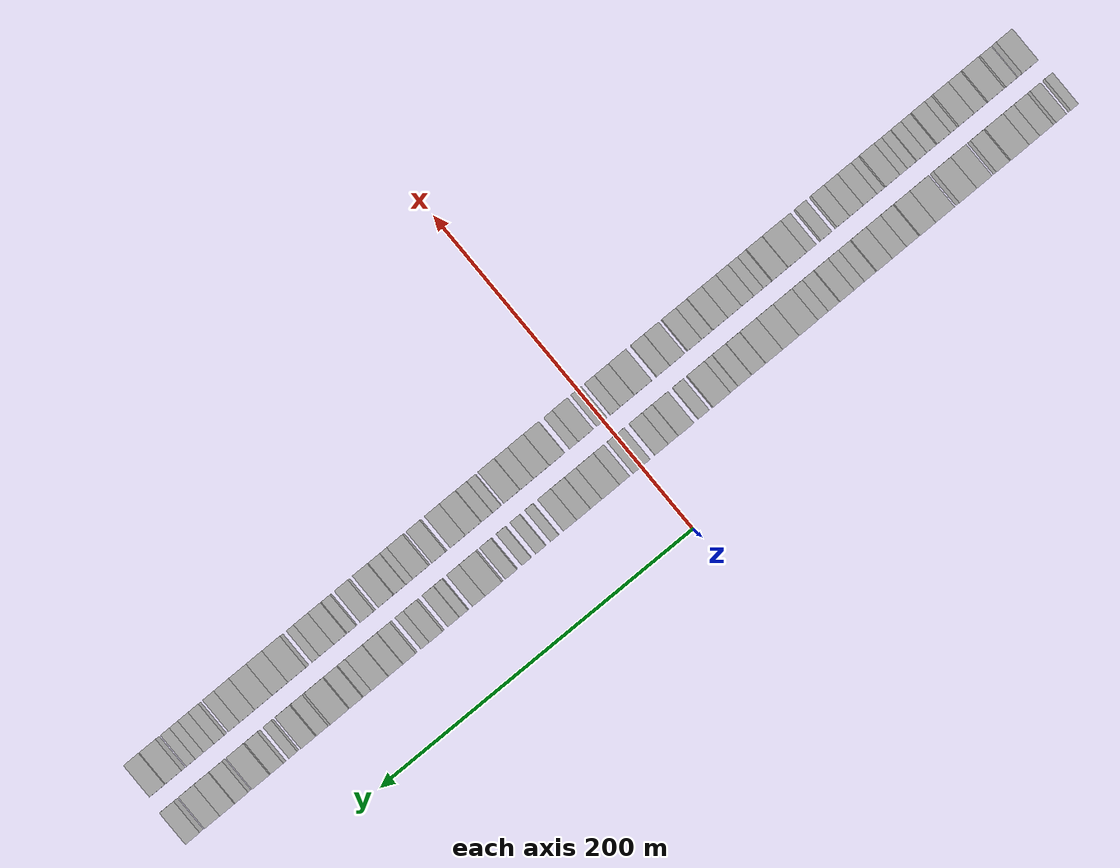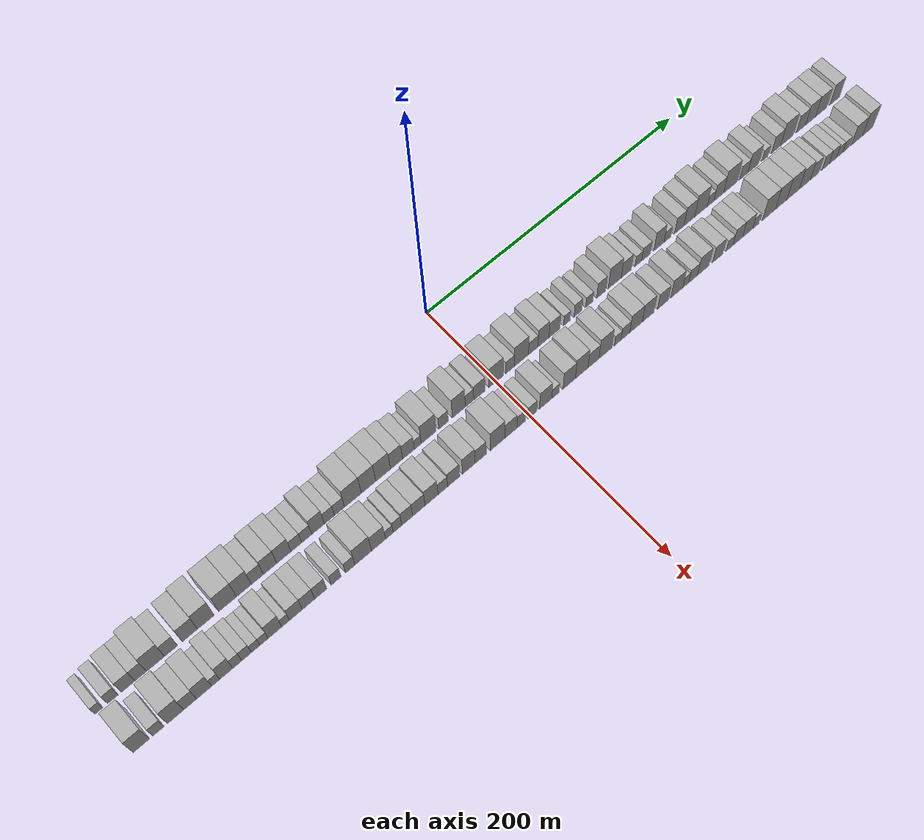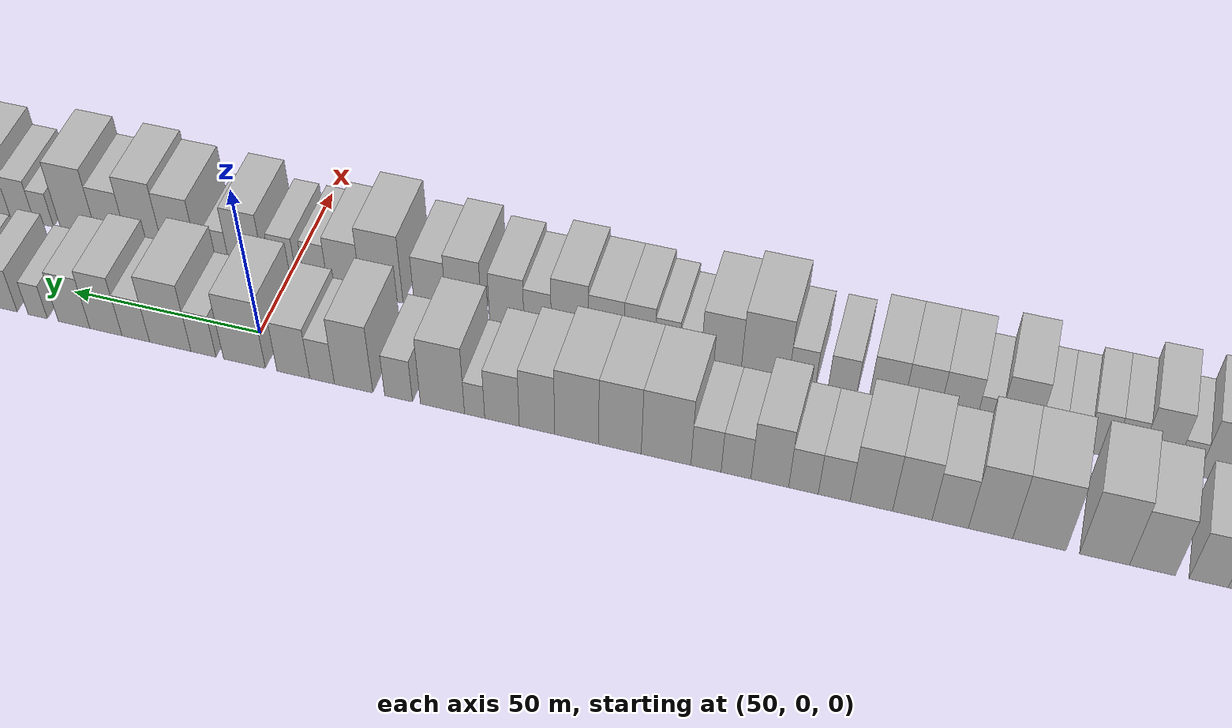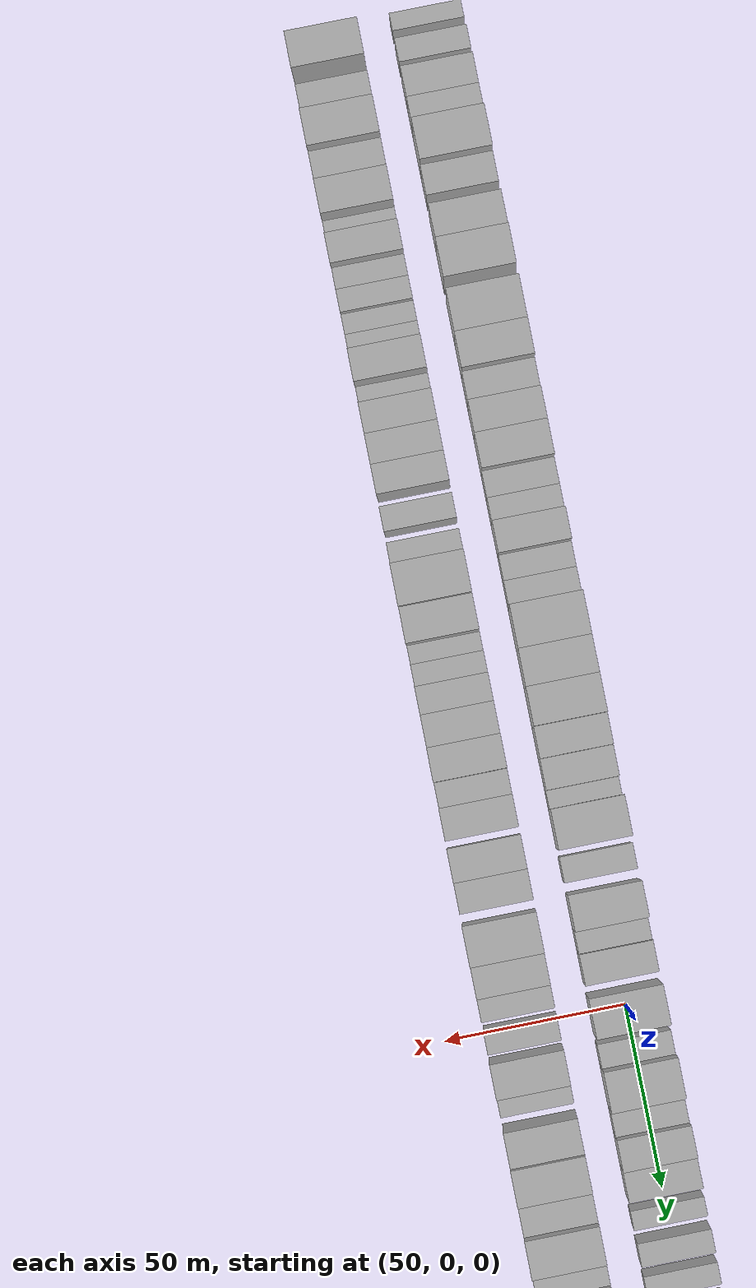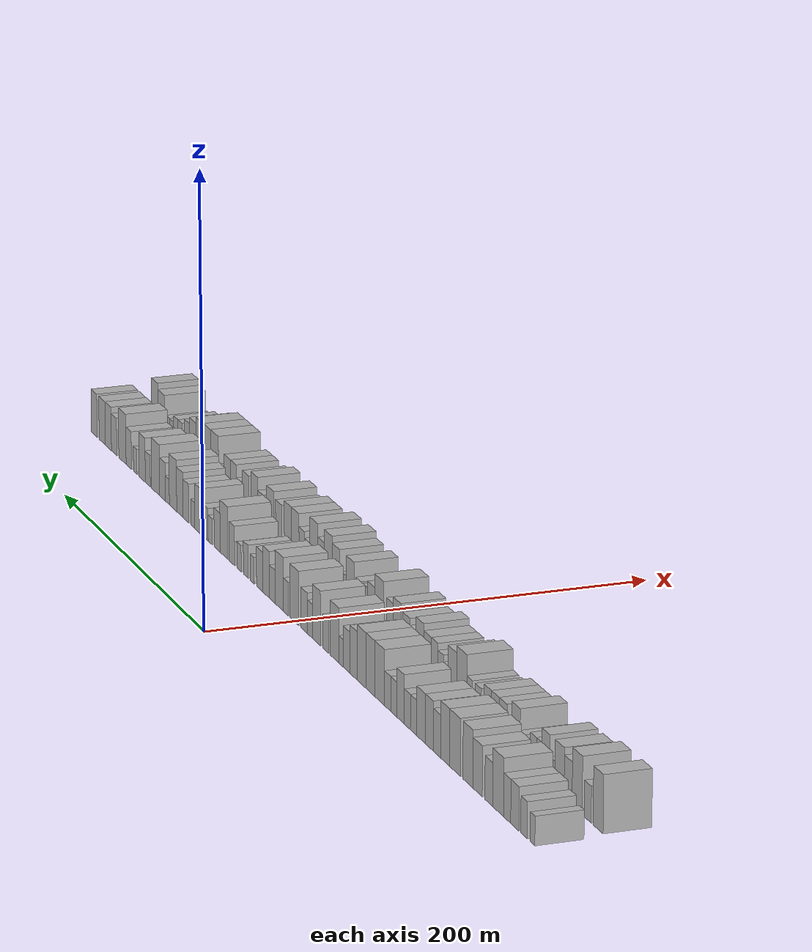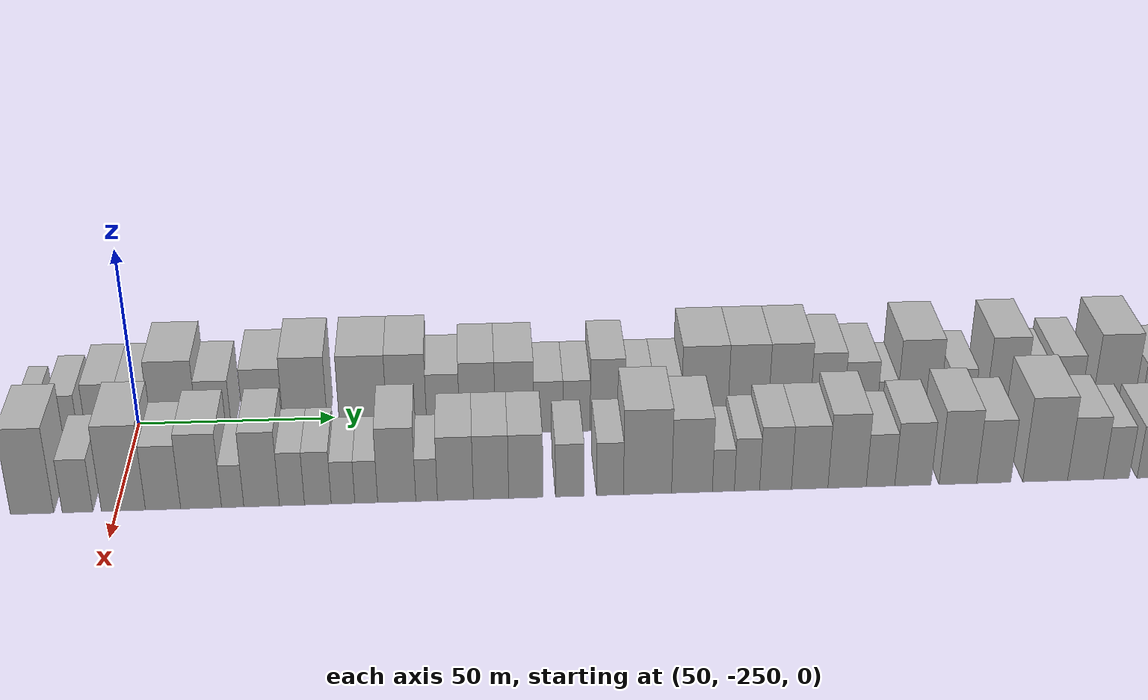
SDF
<sdf version="1.6">
 <world name="default">
  <scene>
   <sky><clouds><speed>12</speed></clouds></sky>
   <ambient>0.4 0.4 0.4 1</ambient>
   <background>0.7 0.7 0.7 1</background>
   <shadows>1</shadows>
  </scene>
  <gravity>0 0 -9.8066</gravity>
  <magnetic_field>6e-06 2.3e-05 -4.2e-05</magnetic_field>
  <physics default="0" name="default_physics" type="ode">
   <ode>
    <solver>
     <type>quick</type>
     <iters>10</iters>
     <sor>1.0</sor>
     <use_dynamic_moi_rescaling>0</use_dynamic_moi_rescaling>
    </solver>
    <constraints>
     <cfm>0</cfm>
     <erp>0.2</erp>
     <contact_max_correcting_vel>100</contact_max_correcting_vel>
     <contact_surface_layer>0.001</contact_surface_layer>
    </constraints>
   </ode>
   <max_step_size>0.004</max_step_size>
   <real_time_factor>1</real_time_factor>
   <real_time_update_rate>250</real_time_update_rate>
  </physics>
  <light name="sun" type="directional">
   <pose>0 0 10 0 0 0</pose>
   <diffuse>0.8 0.8 0.8 1</diffuse>
   <specular>0.2 0.2 0.2 1</specular>
   <attenuation>
    <range>1000</range>
    <constant>0.9</constant>
    <linear>0.01</linear>
    <quadratic>0.001</quadratic>
   </attenuation>
   <direction>-0.5 0.1 -0.9</direction>
  </light>
  <model name="building_1">
   <static>1</static>
   <pose>50.0000 -275.5095 0 0.000000 0.000000 0.000000</pose>
   <link name="link">
    <pose>0 0 6.00 0 0 0</pose>
    <collision name="collision"><geometry><box><size>20.0000 4.9810 12.0000</size></box></geometry></collision>
    <visual name="visual">
     <cast_shadows>0</cast_shadows>
     <geometry><box><size>20.0000 4.9810 12.0000</size></box></geometry>
     <material>
      <script>
       <uri>model://HANNAS_wall/materials/scripts</uri>
       <uri>model://HANNAS_wall/materials/textures</uri>
       <name>vrc/HANNAS_wall</name>
      </script>
     </material>
    </visual>
   </link>
  </model>
  <model name="building_2">
   <static>1</static>
   <pose>50.0000 -266.6562 0 0.000000 0.000000 0.000000</pose>
   <link name="link">
    <pose>0 0 7.50 0 0 0</pose>
    <collision name="collision"><geometry><box><size>20.0000 6.7257 15.0000</size></box></geometry></collision>
    <visual name="visual">
     <cast_shadows>0</cast_shadows>
     <geometry><box><size>20.0000 6.7257 15.0000</size></box></geometry>
     <material>
      <script>
       <uri>model://HANNAS_wall/materials/scripts</uri>
       <uri>model://HANNAS_wall/materials/textures</uri>
       <name>vrc/HANNAS_wall</name>
      </script>
     </material>
    </visual>
   </link>
  </model>
  <model name="building_3">
   <static>1</static>
   <pose>50.0000 -256.9734 0 0.000000 0.000000 0.000000</pose>
   <link name="link">
    <pose>0 0 9.00 0 0 0</pose>
    <collision name="collision"><geometry><box><size>20.0000 8.6398 18.0000</size></box></geometry></collision>
    <visual name="visual">
     <cast_shadows>0</cast_shadows>
     <geometry><box><size>20.0000 8.6398 18.0000</size></box></geometry>
     <material>
      <script>
       <uri>model://HANNAS_wall/materials/scripts</uri>
       <uri>model://HANNAS_wall/materials/textures</uri>
       <name>vrc/HANNAS_wall</name>
      </script>
     </material>
    </visual>
   </link>
  </model>
  <model name="building_4">
   <static>1</static>
   <pose>50.0000 -248.9423 0 0.000000 0.000000 0.000000</pose>
   <link name="link">
    <pose>0 0 9.00 0 0 0</pose>
    <collision name="collision"><geometry><box><size>20.0000 7.4225 18.0000</size></box></geometry></collision>
    <visual name="visual">
     <cast_shadows>0</cast_shadows>
     <geometry><box><size>20.0000 7.4225 18.0000</size></box></geometry>
     <material>
      <script>
       <uri>model://HANNAS_wall/materials/scripts</uri>
       <uri>model://HANNAS_wall/materials/textures</uri>
       <name>vrc/HANNAS_wall</name>
      </script>
     </material>
    </visual>
   </link>
  </model>
  <model name="building_5">
   <static>1</static>
   <pose>50.0000 -239.3968 0 0.000000 0.000000 0.000000</pose>
   <link name="link">
    <pose>0 0 12.00 0 0 0</pose>
    <collision name="collision"><geometry><box><size>20.0000 11.6684 24.0000</size></box></geometry></collision>
    <visual name="visual">
     <cast_shadows>0</cast_shadows>
     <geometry><box><size>20.0000 11.6684 24.0000</size></box></geometry>
     <material>
      <script>
       <uri>model://HANNAS_wall/materials/scripts</uri>
       <uri>model://HANNAS_wall/materials/textures</uri>
       <name>vrc/HANNAS_wall</name>
      </script>
     </material>
    </visual>
   </link>
  </model>
  <model name="building_6">
   <static>1</static>
   <pose>50.0000 -229.3155 0 0.000000 0.000000 0.000000</pose>
   <link name="link">
    <pose>0 0 9.00 0 0 0</pose>
    <collision name="collision"><geometry><box><size>20.0000 8.4943 18.0000</size></box></geometry></collision>
    <visual name="visual">
     <cast_shadows>0</cast_shadows>
     <geometry><box><size>20.0000 8.4943 18.0000</size></box></geometry>
     <material>
      <script>
       <uri>model://HANNAS_wall/materials/scripts</uri>
       <uri>model://HANNAS_wall/materials/textures</uri>
       <name>vrc/HANNAS_wall</name>
      </script>
     </material>
    </visual>
   </link>
  </model>
  <model name="building_7">
   <static>1</static>
   <pose>50.0000 -217.0728 0 0.000000 0.000000 0.000000</pose>
   <link name="link">
    <pose>0 0 10.50 0 0 0</pose>
    <collision name="collision"><geometry><box><size>20.0000 9.9910 21.0000</size></box></geometry></collision>
    <visual name="visual">
     <cast_shadows>0</cast_shadows>
     <geometry><box><size>20.0000 9.9910 21.0000</size></box></geometry>
     <material>
      <script>
       <uri>model://HANNAS_wall/materials/scripts</uri>
       <uri>model://HANNAS_wall/materials/textures</uri>
       <name>vrc/HANNAS_wall</name>
      </script>
     </material>
    </visual>
   </link>
  </model>
  <model name="building_8">
   <static>1</static>
   <pose>50.0000 -206.5521 0 0.000000 0.000000 0.000000</pose>
   <link name="link">
    <pose>0 0 12.00 0 0 0</pose>
    <collision name="collision"><geometry><box><size>20.0000 11.0504 24.0000</size></box></geometry></collision>
    <visual name="visual">
     <cast_shadows>0</cast_shadows>
     <geometry><box><size>20.0000 11.0504 24.0000</size></box></geometry>
     <material>
      <script>
       <uri>model://HANNAS_wall/materials/scripts</uri>
       <uri>model://HANNAS_wall/materials/textures</uri>
       <name>vrc/HANNAS_wall</name>
      </script>
     </material>
    </visual>
   </link>
  </model>
  <model name="building_9">
   <static>1</static>
   <pose>50.0000 -192.0702 0 0.000000 0.000000 0.000000</pose>
   <link name="link">
    <pose>0 0 12.00 0 0 0</pose>
    <collision name="collision"><geometry><box><size>20.0000 11.9134 24.0000</size></box></geometry></collision>
    <visual name="visual">
     <cast_shadows>0</cast_shadows>
     <geometry><box><size>20.0000 11.9134 24.0000</size></box></geometry>
     <material>
      <script>
       <uri>model://HANNAS_wall/materials/scripts</uri>
       <uri>model://HANNAS_wall/materials/textures</uri>
       <name>vrc/HANNAS_wall</name>
      </script>
     </material>
    </visual>
   </link>
  </model>
  <model name="building_10">
   <static>1</static>
   <pose>50.0000 -181.1173 0 0.000000 0.000000 0.000000</pose>
   <link name="link">
    <pose>0 0 12.00 0 0 0</pose>
    <collision name="collision"><geometry><box><size>20.0000 9.9924 24.0000</size></box></geometry></collision>
    <visual name="visual">
     <cast_shadows>0</cast_shadows>
     <geometry><box><size>20.0000 9.9924 24.0000</size></box></geometry>
     <material>
      <script>
       <uri>model://HANNAS_wall/materials/scripts</uri>
       <uri>model://HANNAS_wall/materials/textures</uri>
       <name>vrc/HANNAS_wall</name>
      </script>
     </material>
    </visual>
   </link>
  </model>
  <model name="building_11">
   <static>1</static>
   <pose>50.0000 -171.9731 0 0.000000 0.000000 0.000000</pose>
   <link name="link">
    <pose>0 0 9.00 0 0 0</pose>
    <collision name="collision"><geometry><box><size>20.0000 8.2960 18.0000</size></box></geometry></collision>
    <visual name="visual">
     <cast_shadows>0</cast_shadows>
     <geometry><box><size>20.0000 8.2960 18.0000</size></box></geometry>
     <material>
      <script>
       <uri>model://HANNAS_wall/materials/scripts</uri>
       <uri>model://HANNAS_wall/materials/textures</uri>
       <name>vrc/HANNAS_wall</name>
      </script>
     </material>
    </visual>
   </link>
  </model>
  <model name="building_12">
   <static>1</static>
   <pose>50.0000 -163.3178 0 0.000000 0.000000 0.000000</pose>
   <link name="link">
    <pose>0 0 10.50 0 0 0</pose>
    <collision name="collision"><geometry><box><size>20.0000 9.0146 21.0000</size></box></geometry></collision>
    <visual name="visual">
     <cast_shadows>0</cast_shadows>
     <geometry><box><size>20.0000 9.0146 21.0000</size></box></geometry>
     <material>
      <script>
       <uri>model://HANNAS_wall/materials/scripts</uri>
       <uri>model://HANNAS_wall/materials/textures</uri>
       <name>vrc/HANNAS_wall</name>
      </script>
     </material>
    </visual>
   </link>
  </model>
  <model name="building_13">
   <static>1</static>
   <pose>50.0000 -153.9079 0 0.000000 0.000000 0.000000</pose>
   <link name="link">
    <pose>0 0 10.50 0 0 0</pose>
    <collision name="collision"><geometry><box><size>20.0000 9.8053 21.0000</size></box></geometry></collision>
    <visual name="visual">
     <cast_shadows>0</cast_shadows>
     <geometry><box><size>20.0000 9.8053 21.0000</size></box></geometry>
     <material>
      <script>
       <uri>model://HANNAS_wall/materials/scripts</uri>
       <uri>model://HANNAS_wall/materials/textures</uri>
       <name>vrc/HANNAS_wall</name>
      </script>
     </material>
    </visual>
   </link>
  </model>
  <model name="building_14">
   <static>1</static>
   <pose>50.0000 -145.3055 0 0.000000 0.000000 0.000000</pose>
   <link name="link">
    <pose>0 0 7.50 0 0 0</pose>
    <collision name="collision"><geometry><box><size>20.0000 7.3994 15.0000</size></box></geometry></collision>
    <visual name="visual">
     <cast_shadows>0</cast_shadows>
     <geometry><box><size>20.0000 7.3994 15.0000</size></box></geometry>
     <material>
      <script>
       <uri>model://HANNAS_wall/materials/scripts</uri>
       <uri>model://HANNAS_wall/materials/textures</uri>
       <name>vrc/HANNAS_wall</name>
      </script>
     </material>
    </visual>
   </link>
  </model>
  <model name="building_15">
   <static>1</static>
   <pose>50.0000 -138.1473 0 0.000000 0.000000 0.000000</pose>
   <link name="link">
    <pose>0 0 7.50 0 0 0</pose>
    <collision name="collision"><geometry><box><size>20.0000 6.9170 15.0000</size></box></geometry></collision>
    <visual name="visual">
     <cast_shadows>0</cast_shadows>
     <geometry><box><size>20.0000 6.9170 15.0000</size></box></geometry>
     <material>
      <script>
       <uri>model://HANNAS_wall/materials/scripts</uri>
       <uri>model://HANNAS_wall/materials/textures</uri>
       <name>vrc/HANNAS_wall</name>
      </script>
     </material>
    </visual>
   </link>
  </model>
  <model name="building_16">
   <static>1</static>
   <pose>50.0000 -130.2422 0 0.000000 0.000000 0.000000</pose>
   <link name="link">
    <pose>0 0 10.50 0 0 0</pose>
    <collision name="collision"><geometry><box><size>20.0000 8.8931 21.0000</size></box></geometry></collision>
    <visual name="visual">
     <cast_shadows>0</cast_shadows>
     <geometry><box><size>20.0000 8.8931 21.0000</size></box></geometry>
     <material>
      <script>
       <uri>model://HANNAS_wall/materials/scripts</uri>
       <uri>model://HANNAS_wall/materials/textures</uri>
       <name>vrc/HANNAS_wall</name>
      </script>
     </material>
    </visual>
   </link>
  </model>
  <model name="building_17">
   <static>1</static>
   <pose>50.0000 -122.2671 0 0.000000 0.000000 0.000000</pose>
   <link name="link">
    <pose>0 0 7.50 0 0 0</pose>
    <collision name="collision"><geometry><box><size>20.0000 7.0571 15.0000</size></box></geometry></collision>
    <visual name="visual">
     <cast_shadows>0</cast_shadows>
     <geometry><box><size>20.0000 7.0571 15.0000</size></box></geometry>
     <material>
      <script>
       <uri>model://HANNAS_wall/materials/scripts</uri>
       <uri>model://HANNAS_wall/materials/textures</uri>
       <name>vrc/HANNAS_wall</name>
      </script>
     </material>
    </visual>
   </link>
  </model>
  <model name="building_18">
   <static>1</static>
   <pose>50.0000 -115.1416 0 0.000000 0.000000 0.000000</pose>
   <link name="link">
    <pose>0 0 7.50 0 0 0</pose>
    <collision name="collision"><geometry><box><size>20.0000 7.1939 15.0000</size></box></geometry></collision>
    <visual name="visual">
     <cast_shadows>0</cast_shadows>
     <geometry><box><size>20.0000 7.1939 15.0000</size></box></geometry>
     <material>
      <script>
       <uri>model://HANNAS_wall/materials/scripts</uri>
       <uri>model://HANNAS_wall/materials/textures</uri>
       <name>vrc/HANNAS_wall</name>
      </script>
     </material>
    </visual>
   </link>
  </model>
  <model name="building_19">
   <static>1</static>
   <pose>50.0000 -105.5763 0 0.000000 0.000000 0.000000</pose>
   <link name="link">
    <pose>0 0 12.00 0 0 0</pose>
    <collision name="collision"><geometry><box><size>20.0000 11.9367 24.0000</size></box></geometry></collision>
    <visual name="visual">
     <cast_shadows>0</cast_shadows>
     <geometry><box><size>20.0000 11.9367 24.0000</size></box></geometry>
     <material>
      <script>
       <uri>model://HANNAS_wall/materials/scripts</uri>
       <uri>model://HANNAS_wall/materials/textures</uri>
       <name>vrc/HANNAS_wall</name>
      </script>
     </material>
    </visual>
   </link>
  </model>
  <model name="building_20">
   <static>1</static>
   <pose>50.0000 -94.4235 0 0.000000 0.000000 0.000000</pose>
   <link name="link">
    <pose>0 0 12.00 0 0 0</pose>
    <collision name="collision"><geometry><box><size>20.0000 10.3688 24.0000</size></box></geometry></collision>
    <visual name="visual">
     <cast_shadows>0</cast_shadows>
     <geometry><box><size>20.0000 10.3688 24.0000</size></box></geometry>
     <material>
      <script>
       <uri>model://HANNAS_wall/materials/scripts</uri>
       <uri>model://HANNAS_wall/materials/textures</uri>
       <name>vrc/HANNAS_wall</name>
      </script>
     </material>
    </visual>
   </link>
  </model>
  <model name="building_21">
   <static>1</static>
   <pose>50.0000 -83.8943 0 0.000000 0.000000 0.000000</pose>
   <link name="link">
    <pose>0 0 12.00 0 0 0</pose>
    <collision name="collision"><geometry><box><size>20.0000 10.6895 24.0000</size></box></geometry></collision>
    <visual name="visual">
     <cast_shadows>0</cast_shadows>
     <geometry><box><size>20.0000 10.6895 24.0000</size></box></geometry>
     <material>
      <script>
       <uri>model://HANNAS_wall/materials/scripts</uri>
       <uri>model://HANNAS_wall/materials/textures</uri>
       <name>vrc/HANNAS_wall</name>
      </script>
     </material>
    </visual>
   </link>
  </model>
  <model name="building_22">
   <static>1</static>
   <pose>50.0000 -74.1947 0 0.000000 0.000000 0.000000</pose>
   <link name="link">
    <pose>0 0 10.50 0 0 0</pose>
    <collision name="collision"><geometry><box><size>20.0000 8.7096 21.0000</size></box></geometry></collision>
    <visual name="visual">
     <cast_shadows>0</cast_shadows>
     <geometry><box><size>20.0000 8.7096 21.0000</size></box></geometry>
     <material>
      <script>
       <uri>model://HANNAS_wall/materials/scripts</uri>
       <uri>model://HANNAS_wall/materials/textures</uri>
       <name>vrc/HANNAS_wall</name>
      </script>
     </material>
    </visual>
   </link>
  </model>
  <model name="building_23">
   <static>1</static>
   <pose>50.0000 -65.5547 0 0.000000 0.000000 0.000000</pose>
   <link name="link">
    <pose>0 0 9.00 0 0 0</pose>
    <collision name="collision"><geometry><box><size>20.0000 8.5704 18.0000</size></box></geometry></collision>
    <visual name="visual">
     <cast_shadows>0</cast_shadows>
     <geometry><box><size>20.0000 8.5704 18.0000</size></box></geometry>
     <material>
      <script>
       <uri>model://HANNAS_wall/materials/scripts</uri>
       <uri>model://HANNAS_wall/materials/textures</uri>
       <name>vrc/HANNAS_wall</name>
      </script>
     </material>
    </visual>
   </link>
  </model>
  <model name="building_24">
   <static>1</static>
   <pose>50.0000 -58.7450 0 0.000000 0.000000 0.000000</pose>
   <link name="link">
    <pose>0 0 6.00 0 0 0</pose>
    <collision name="collision"><geometry><box><size>20.0000 5.0491 12.0000</size></box></geometry></collision>
    <visual name="visual">
     <cast_shadows>0</cast_shadows>
     <geometry><box><size>20.0000 5.0491 12.0000</size></box></geometry>
     <material>
      <script>
       <uri>model://HANNAS_wall/materials/scripts</uri>
       <uri>model://HANNAS_wall/materials/textures</uri>
       <name>vrc/HANNAS_wall</name>
      </script>
     </material>
    </visual>
   </link>
  </model>
  <model name="building_25">
   <static>1</static>
   <pose>50.0000 -50.6894 0 0.000000 0.000000 0.000000</pose>
   <link name="link">
    <pose>0 0 12.00 0 0 0</pose>
    <collision name="collision"><geometry><box><size>20.0000 11.0620 24.0000</size></box></geometry></collision>
    <visual name="visual">
     <cast_shadows>0</cast_shadows>
     <geometry><box><size>20.0000 11.0620 24.0000</size></box></geometry>
     <material>
      <script>
       <uri>model://HANNAS_wall/materials/scripts</uri>
       <uri>model://HANNAS_wall/materials/textures</uri>
       <name>vrc/HANNAS_wall</name>
      </script>
     </material>
    </visual>
   </link>
  </model>
  <model name="building_26">
   <static>1</static>
   <pose>50.0000 -39.6326 0 0.000000 0.000000 0.000000</pose>
   <link name="link">
    <pose>0 0 7.50 0 0 0</pose>
    <collision name="collision"><geometry><box><size>20.0000 7.0516 15.0000</size></box></geometry></collision>
    <visual name="visual">
     <cast_shadows>0</cast_shadows>
     <geometry><box><size>20.0000 7.0516 15.0000</size></box></geometry>
     <material>
      <script>
       <uri>model://HANNAS_wall/materials/scripts</uri>
       <uri>model://HANNAS_wall/materials/textures</uri>
       <name>vrc/HANNAS_wall</name>
      </script>
     </material>
    </visual>
   </link>
  </model>
  <model name="building_27">
   <static>1</static>
   <pose>50.0000 -28.1951 0 0.000000 0.000000 0.000000</pose>
   <link name="link">
    <pose>0 0 12.00 0 0 0</pose>
    <collision name="collision"><geometry><box><size>20.0000 9.8236 24.0000</size></box></geometry></collision>
    <visual name="visual">
     <cast_shadows>0</cast_shadows>
     <geometry><box><size>20.0000 9.8236 24.0000</size></box></geometry>
     <material>
      <script>
       <uri>model://HANNAS_wall/materials/scripts</uri>
       <uri>model://HANNAS_wall/materials/textures</uri>
       <name>vrc/HANNAS_wall</name>
      </script>
     </material>
    </visual>
   </link>
  </model>
  <model name="building_28">
   <static>1</static>
   <pose>50.0000 -20.1003 0 0.000000 0.000000 0.000000</pose>
   <link name="link">
    <pose>0 0 7.50 0 0 0</pose>
    <collision name="collision"><geometry><box><size>20.0000 6.3659 15.0000</size></box></geometry></collision>
    <visual name="visual">
     <cast_shadows>0</cast_shadows>
     <geometry><box><size>20.0000 6.3659 15.0000</size></box></geometry>
     <material>
      <script>
       <uri>model://HANNAS_wall/materials/scripts</uri>
       <uri>model://HANNAS_wall/materials/textures</uri>
       <name>vrc/HANNAS_wall</name>
      </script>
     </material>
    </visual>
   </link>
  </model>
  <model name="building_29">
   <static>1</static>
   <pose>50.0000 -12.6781 0 0.000000 0.000000 0.000000</pose>
   <link name="link">
    <pose>0 0 9.00 0 0 0</pose>
    <collision name="collision"><geometry><box><size>20.0000 8.4785 18.0000</size></box></geometry></collision>
    <visual name="visual">
     <cast_shadows>0</cast_shadows>
     <geometry><box><size>20.0000 8.4785 18.0000</size></box></geometry>
     <material>
      <script>
       <uri>model://HANNAS_wall/materials/scripts</uri>
       <uri>model://HANNAS_wall/materials/textures</uri>
       <name>vrc/HANNAS_wall</name>
      </script>
     </material>
    </visual>
   </link>
  </model>
  <model name="building_30">
   <static>1</static>
   <pose>50.0000 0.0246 0 0.000000 0.000000 0.000000</pose>
   <link name="link">
    <pose>0 0 12.00 0 0 0</pose>
    <collision name="collision"><geometry><box><size>20.0000 10.9269 24.0000</size></box></geometry></collision>
    <visual name="visual">
     <cast_shadows>0</cast_shadows>
     <geometry><box><size>20.0000 10.9269 24.0000</size></box></geometry>
     <material>
      <script>
       <uri>model://HANNAS_wall/materials/scripts</uri>
       <uri>model://HANNAS_wall/materials/textures</uri>
       <name>vrc/HANNAS_wall</name>
      </script>
     </material>
    </visual>
   </link>
  </model>
  <model name="building_31">
   <static>1</static>
   <pose>50.0000 10.7795 0 0.000000 0.000000 0.000000</pose>
   <link name="link">
    <pose>0 0 7.50 0 0 0</pose>
    <collision name="collision"><geometry><box><size>20.0000 6.5830 15.0000</size></box></geometry></collision>
    <visual name="visual">
     <cast_shadows>0</cast_shadows>
     <geometry><box><size>20.0000 6.5830 15.0000</size></box></geometry>
     <material>
      <script>
       <uri>model://HANNAS_wall/materials/scripts</uri>
       <uri>model://HANNAS_wall/materials/textures</uri>
       <name>vrc/HANNAS_wall</name>
      </script>
     </material>
    </visual>
   </link>
  </model>
  <model name="building_32">
   <static>1</static>
   <pose>50.0000 19.5707 0 0.000000 0.000000 0.000000</pose>
   <link name="link">
    <pose>0 0 12.00 0 0 0</pose>
    <collision name="collision"><geometry><box><size>20.0000 10.9994 24.0000</size></box></geometry></collision>
    <visual name="visual">
     <cast_shadows>0</cast_shadows>
     <geometry><box><size>20.0000 10.9994 24.0000</size></box></geometry>
     <material>
      <script>
       <uri>model://HANNAS_wall/materials/scripts</uri>
       <uri>model://HANNAS_wall/materials/textures</uri>
       <name>vrc/HANNAS_wall</name>
      </script>
     </material>
    </visual>
   </link>
  </model>
  <model name="building_33">
   <static>1</static>
   <pose>50.0000 28.7614 0 0.000000 0.000000 0.000000</pose>
   <link name="link">
    <pose>0 0 7.50 0 0 0</pose>
    <collision name="collision"><geometry><box><size>20.0000 7.3819 15.0000</size></box></geometry></collision>
    <visual name="visual">
     <cast_shadows>0</cast_shadows>
     <geometry><box><size>20.0000 7.3819 15.0000</size></box></geometry>
     <material>
      <script>
       <uri>model://HANNAS_wall/materials/scripts</uri>
       <uri>model://HANNAS_wall/materials/textures</uri>
       <name>vrc/HANNAS_wall</name>
      </script>
     </material>
    </visual>
   </link>
  </model>
  <model name="building_34">
   <static>1</static>
   <pose>50.0000 36.7745 0 0.000000 0.000000 0.000000</pose>
   <link name="link">
    <pose>0 0 10.50 0 0 0</pose>
    <collision name="collision"><geometry><box><size>20.0000 8.6443 21.0000</size></box></geometry></collision>
    <visual name="visual">
     <cast_shadows>0</cast_shadows>
     <geometry><box><size>20.0000 8.6443 21.0000</size></box></geometry>
     <material>
      <script>
       <uri>model://HANNAS_wall/materials/scripts</uri>
       <uri>model://HANNAS_wall/materials/textures</uri>
       <name>vrc/HANNAS_wall</name>
      </script>
     </material>
    </visual>
   </link>
  </model>
  <model name="building_35">
   <static>1</static>
   <pose>50.0000 45.3542 0 0.000000 0.000000 0.000000</pose>
   <link name="link">
    <pose>0 0 9.00 0 0 0</pose>
    <collision name="collision"><geometry><box><size>20.0000 8.5152 18.0000</size></box></geometry></collision>
    <visual name="visual">
     <cast_shadows>0</cast_shadows>
     <geometry><box><size>20.0000 8.5152 18.0000</size></box></geometry>
     <material>
      <script>
       <uri>model://HANNAS_wall/materials/scripts</uri>
       <uri>model://HANNAS_wall/materials/textures</uri>
       <name>vrc/HANNAS_wall</name>
      </script>
     </material>
    </visual>
   </link>
  </model>
  <model name="building_36">
   <static>1</static>
   <pose>50.0000 55.2423 0 0.000000 0.000000 0.000000</pose>
   <link name="link">
    <pose>0 0 6.00 0 0 0</pose>
    <collision name="collision"><geometry><box><size>20.0000 5.2609 12.0000</size></box></geometry></collision>
    <visual name="visual">
     <cast_shadows>0</cast_shadows>
     <geometry><box><size>20.0000 5.2609 12.0000</size></box></geometry>
     <material>
      <script>
       <uri>model://HANNAS_wall/materials/scripts</uri>
       <uri>model://HANNAS_wall/materials/textures</uri>
       <name>vrc/HANNAS_wall</name>
      </script>
     </material>
    </visual>
   </link>
  </model>
  <model name="building_37">
   <static>1</static>
   <pose>50.0000 64.0448 0 0.000000 0.000000 0.000000</pose>
   <link name="link">
    <pose>0 0 7.50 0 0 0</pose>
    <collision name="collision"><geometry><box><size>20.0000 6.3442 15.0000</size></box></geometry></collision>
    <visual name="visual">
     <cast_shadows>0</cast_shadows>
     <geometry><box><size>20.0000 6.3442 15.0000</size></box></geometry>
     <material>
      <script>
       <uri>model://HANNAS_wall/materials/scripts</uri>
       <uri>model://HANNAS_wall/materials/textures</uri>
       <name>vrc/HANNAS_wall</name>
      </script>
     </material>
    </visual>
   </link>
  </model>
  <model name="building_38">
   <static>1</static>
   <pose>50.0000 73.1674 0 0.000000 0.000000 0.000000</pose>
   <link name="link">
    <pose>0 0 6.00 0 0 0</pose>
    <collision name="collision"><geometry><box><size>20.0000 5.9009 12.0000</size></box></geometry></collision>
    <visual name="visual">
     <cast_shadows>0</cast_shadows>
     <geometry><box><size>20.0000 5.9009 12.0000</size></box></geometry>
     <material>
      <script>
       <uri>model://HANNAS_wall/materials/scripts</uri>
       <uri>model://HANNAS_wall/materials/textures</uri>
       <name>vrc/HANNAS_wall</name>
      </script>
     </material>
    </visual>
   </link>
  </model>
  <model name="building_39">
   <static>1</static>
   <pose>50.0000 82.7733 0 0.000000 0.000000 0.000000</pose>
   <link name="link">
    <pose>0 0 9.00 0 0 0</pose>
    <collision name="collision"><geometry><box><size>20.0000 7.3110 18.0000</size></box></geometry></collision>
    <visual name="visual">
     <cast_shadows>0</cast_shadows>
     <geometry><box><size>20.0000 7.3110 18.0000</size></box></geometry>
     <material>
      <script>
       <uri>model://HANNAS_wall/materials/scripts</uri>
       <uri>model://HANNAS_wall/materials/textures</uri>
       <name>vrc/HANNAS_wall</name>
      </script>
     </material>
    </visual>
   </link>
  </model>
  <model name="building_40">
   <static>1</static>
   <pose>50.0000 93.7468 0 0.000000 0.000000 0.000000</pose>
   <link name="link">
    <pose>0 0 12.00 0 0 0</pose>
    <collision name="collision"><geometry><box><size>20.0000 10.6359 24.0000</size></box></geometry></collision>
    <visual name="visual">
     <cast_shadows>0</cast_shadows>
     <geometry><box><size>20.0000 10.6359 24.0000</size></box></geometry>
     <material>
      <script>
       <uri>model://HANNAS_wall/materials/scripts</uri>
       <uri>model://HANNAS_wall/materials/textures</uri>
       <name>vrc/HANNAS_wall</name>
      </script>
     </material>
    </visual>
   </link>
  </model>
  <model name="building_41">
   <static>1</static>
   <pose>50.0000 103.1954 0 0.000000 0.000000 0.000000</pose>
   <link name="link">
    <pose>0 0 9.00 0 0 0</pose>
    <collision name="collision"><geometry><box><size>20.0000 8.2614 18.0000</size></box></geometry></collision>
    <visual name="visual">
     <cast_shadows>0</cast_shadows>
     <geometry><box><size>20.0000 8.2614 18.0000</size></box></geometry>
     <material>
      <script>
       <uri>model://HANNAS_wall/materials/scripts</uri>
       <uri>model://HANNAS_wall/materials/textures</uri>
       <name>vrc/HANNAS_wall</name>
      </script>
     </material>
    </visual>
   </link>
  </model>
  <model name="building_42">
   <static>1</static>
   <pose>50.0000 113.0669 0 0.000000 0.000000 0.000000</pose>
   <link name="link">
    <pose>0 0 6.00 0 0 0</pose>
    <collision name="collision"><geometry><box><size>20.0000 5.4815 12.0000</size></box></geometry></collision>
    <visual name="visual">
     <cast_shadows>0</cast_shadows>
     <geometry><box><size>20.0000 5.4815 12.0000</size></box></geometry>
     <material>
      <script>
       <uri>model://HANNAS_wall/materials/scripts</uri>
       <uri>model://HANNAS_wall/materials/textures</uri>
       <name>vrc/HANNAS_wall</name>
      </script>
     </material>
    </visual>
   </link>
  </model>
  <model name="building_43">
   <static>1</static>
   <pose>50.0000 119.4377 0 0.000000 0.000000 0.000000</pose>
   <link name="link">
    <pose>0 0 7.50 0 0 0</pose>
    <collision name="collision"><geometry><box><size>20.0000 7.2602 15.0000</size></box></geometry></collision>
    <visual name="visual">
     <cast_shadows>0</cast_shadows>
     <geometry><box><size>20.0000 7.2602 15.0000</size></box></geometry>
     <material>
      <script>
       <uri>model://HANNAS_wall/materials/scripts</uri>
       <uri>model://HANNAS_wall/materials/textures</uri>
       <name>vrc/HANNAS_wall</name>
      </script>
     </material>
    </visual>
   </link>
  </model>
  <model name="building_44">
   <static>1</static>
   <pose>50.0000 130.3110 0 0.000000 0.000000 0.000000</pose>
   <link name="link">
    <pose>0 0 10.50 0 0 0</pose>
    <collision name="collision"><geometry><box><size>20.0000 8.4865 21.0000</size></box></geometry></collision>
    <visual name="visual">
     <cast_shadows>0</cast_shadows>
     <geometry><box><size>20.0000 8.4865 21.0000</size></box></geometry>
     <material>
      <script>
       <uri>model://HANNAS_wall/materials/scripts</uri>
       <uri>model://HANNAS_wall/materials/textures</uri>
       <name>vrc/HANNAS_wall</name>
      </script>
     </material>
    </visual>
   </link>
  </model>
  <model name="building_45">
   <static>1</static>
   <pose>50.0000 137.4243 0 0.000000 0.000000 0.000000</pose>
   <link name="link">
    <pose>0 0 6.00 0 0 0</pose>
    <collision name="collision"><geometry><box><size>20.0000 5.7400 12.0000</size></box></geometry></collision>
    <visual name="visual">
     <cast_shadows>0</cast_shadows>
     <geometry><box><size>20.0000 5.7400 12.0000</size></box></geometry>
     <material>
      <script>
       <uri>model://HANNAS_wall/materials/scripts</uri>
       <uri>model://HANNAS_wall/materials/textures</uri>
       <name>vrc/HANNAS_wall</name>
      </script>
     </material>
    </visual>
   </link>
  </model>
  <model name="building_46">
   <static>1</static>
   <pose>50.0000 147.2909 0 0.000000 0.000000 0.000000</pose>
   <link name="link">
    <pose>0 0 9.00 0 0 0</pose>
    <collision name="collision"><geometry><box><size>20.0000 7.9932 18.0000</size></box></geometry></collision>
    <visual name="visual">
     <cast_shadows>0</cast_shadows>
     <geometry><box><size>20.0000 7.9932 18.0000</size></box></geometry>
     <material>
      <script>
       <uri>model://HANNAS_wall/materials/scripts</uri>
       <uri>model://HANNAS_wall/materials/textures</uri>
       <name>vrc/HANNAS_wall</name>
      </script>
     </material>
    </visual>
   </link>
  </model>
  <model name="building_47">
   <static>1</static>
   <pose>50.0000 155.8507 0 0.000000 0.000000 0.000000</pose>
   <link name="link">
    <pose>0 0 10.50 0 0 0</pose>
    <collision name="collision"><geometry><box><size>20.0000 9.1264 21.0000</size></box></geometry></collision>
    <visual name="visual">
     <cast_shadows>0</cast_shadows>
     <geometry><box><size>20.0000 9.1264 21.0000</size></box></geometry>
     <material>
      <script>
       <uri>model://HANNAS_wall/materials/scripts</uri>
       <uri>model://HANNAS_wall/materials/textures</uri>
       <name>vrc/HANNAS_wall</name>
      </script>
     </material>
    </visual>
   </link>
  </model>
  <model name="building_48">
   <static>1</static>
   <pose>50.0000 165.7741 0 0.000000 0.000000 0.000000</pose>
   <link name="link">
    <pose>0 0 12.00 0 0 0</pose>
    <collision name="collision"><geometry><box><size>20.0000 10.7204 24.0000</size></box></geometry></collision>
    <visual name="visual">
     <cast_shadows>0</cast_shadows>
     <geometry><box><size>20.0000 10.7204 24.0000</size></box></geometry>
     <material>
      <script>
       <uri>model://HANNAS_wall/materials/scripts</uri>
       <uri>model://HANNAS_wall/materials/textures</uri>
       <name>vrc/HANNAS_wall</name>
      </script>
     </material>
    </visual>
   </link>
  </model>
  <model name="building_49">
   <static>1</static>
   <pose>50.0000 174.0424 0 0.000000 0.000000 0.000000</pose>
   <link name="link">
    <pose>0 0 6.00 0 0 0</pose>
    <collision name="collision"><geometry><box><size>20.0000 5.8160 12.0000</size></box></geometry></collision>
    <visual name="visual">
     <cast_shadows>0</cast_shadows>
     <geometry><box><size>20.0000 5.8160 12.0000</size></box></geometry>
     <material>
      <script>
       <uri>model://HANNAS_wall/materials/scripts</uri>
       <uri>model://HANNAS_wall/materials/textures</uri>
       <name>vrc/HANNAS_wall</name>
      </script>
     </material>
    </visual>
   </link>
  </model>
  <model name="building_50">
   <static>1</static>
   <pose>50.0000 181.1115 0 0.000000 0.000000 0.000000</pose>
   <link name="link">
    <pose>0 0 9.00 0 0 0</pose>
    <collision name="collision"><geometry><box><size>20.0000 8.3222 18.0000</size></box></geometry></collision>
    <visual name="visual">
     <cast_shadows>0</cast_shadows>
     <geometry><box><size>20.0000 8.3222 18.0000</size></box></geometry>
     <material>
      <script>
       <uri>model://HANNAS_wall/materials/scripts</uri>
       <uri>model://HANNAS_wall/materials/textures</uri>
       <name>vrc/HANNAS_wall</name>
      </script>
     </material>
    </visual>
   </link>
  </model>
  <model name="building_51">
   <static>1</static>
   <pose>50.0000 191.1961 0 0.000000 0.000000 0.000000</pose>
   <link name="link">
    <pose>0 0 12.00 0 0 0</pose>
    <collision name="collision"><geometry><box><size>20.0000 11.8470 24.0000</size></box></geometry></collision>
    <visual name="visual">
     <cast_shadows>0</cast_shadows>
     <geometry><box><size>20.0000 11.8470 24.0000</size></box></geometry>
     <material>
      <script>
       <uri>model://HANNAS_wall/materials/scripts</uri>
       <uri>model://HANNAS_wall/materials/textures</uri>
       <name>vrc/HANNAS_wall</name>
      </script>
     </material>
    </visual>
   </link>
  </model>
  <model name="building_52">
   <static>1</static>
   <pose>50.0000 202.8161 0 0.000000 0.000000 0.000000</pose>
   <link name="link">
    <pose>0 0 7.50 0 0 0</pose>
    <collision name="collision"><geometry><box><size>20.0000 7.3930 15.0000</size></box></geometry></collision>
    <visual name="visual">
     <cast_shadows>0</cast_shadows>
     <geometry><box><size>20.0000 7.3930 15.0000</size></box></geometry>
     <material>
      <script>
       <uri>model://HANNAS_wall/materials/scripts</uri>
       <uri>model://HANNAS_wall/materials/textures</uri>
       <name>vrc/HANNAS_wall</name>
      </script>
     </material>
    </visual>
   </link>
  </model>
  <model name="building_53">
   <static>1</static>
   <pose>50.0000 211.2245 0 0.000000 0.000000 0.000000</pose>
   <link name="link">
    <pose>0 0 10.50 0 0 0</pose>
    <collision name="collision"><geometry><box><size>20.0000 9.4239 21.0000</size></box></geometry></collision>
    <visual name="visual">
     <cast_shadows>0</cast_shadows>
     <geometry><box><size>20.0000 9.4239 21.0000</size></box></geometry>
     <material>
      <script>
       <uri>model://HANNAS_wall/materials/scripts</uri>
       <uri>model://HANNAS_wall/materials/textures</uri>
       <name>vrc/HANNAS_wall</name>
      </script>
     </material>
    </visual>
   </link>
  </model>
  <model name="building_54">
   <static>1</static>
   <pose>50.0000 221.6226 0 0.000000 0.000000 0.000000</pose>
   <link name="link">
    <pose>0 0 6.00 0 0 0</pose>
    <collision name="collision"><geometry><box><size>20.0000 5.3722 12.0000</size></box></geometry></collision>
    <visual name="visual">
     <cast_shadows>0</cast_shadows>
     <geometry><box><size>20.0000 5.3722 12.0000</size></box></geometry>
     <material>
      <script>
       <uri>model://HANNAS_wall/materials/scripts</uri>
       <uri>model://HANNAS_wall/materials/textures</uri>
       <name>vrc/HANNAS_wall</name>
      </script>
     </material>
    </visual>
   </link>
  </model>
  <model name="building_55">
   <static>1</static>
   <pose>50.0000 231.4032 0 0.000000 0.000000 0.000000</pose>
   <link name="link">
    <pose>0 0 9.00 0 0 0</pose>
    <collision name="collision"><geometry><box><size>20.0000 8.1891 18.0000</size></box></geometry></collision>
    <visual name="visual">
     <cast_shadows>0</cast_shadows>
     <geometry><box><size>20.0000 8.1891 18.0000</size></box></geometry>
     <material>
      <script>
       <uri>model://HANNAS_wall/materials/scripts</uri>
       <uri>model://HANNAS_wall/materials/textures</uri>
       <name>vrc/HANNAS_wall</name>
      </script>
     </material>
    </visual>
   </link>
  </model>
  <model name="building_56">
   <static>1</static>
   <pose>50.0000 241.0677 0 0.000000 0.000000 0.000000</pose>
   <link name="link">
    <pose>0 0 12.00 0 0 0</pose>
    <collision name="collision"><geometry><box><size>20.0000 11.1399 24.0000</size></box></geometry></collision>
    <visual name="visual">
     <cast_shadows>0</cast_shadows>
     <geometry><box><size>20.0000 11.1399 24.0000</size></box></geometry>
     <material>
      <script>
       <uri>model://HANNAS_wall/materials/scripts</uri>
       <uri>model://HANNAS_wall/materials/textures</uri>
       <name>vrc/HANNAS_wall</name>
      </script>
     </material>
    </visual>
   </link>
  </model>
  <model name="building_57">
   <static>1</static>
   <pose>50.0000 253.7902 0 0.000000 0.000000 0.000000</pose>
   <link name="link">
    <pose>0 0 9.00 0 0 0</pose>
    <collision name="collision"><geometry><box><size>20.0000 8.3051 18.0000</size></box></geometry></collision>
    <visual name="visual">
     <cast_shadows>0</cast_shadows>
     <geometry><box><size>20.0000 8.3051 18.0000</size></box></geometry>
     <material>
      <script>
       <uri>model://HANNAS_wall/materials/scripts</uri>
       <uri>model://HANNAS_wall/materials/textures</uri>
       <name>vrc/HANNAS_wall</name>
      </script>
     </material>
    </visual>
   </link>
  </model>
  <model name="building_58">
   <static>1</static>
   <pose>50.0000 262.6030 0 0.000000 0.000000 0.000000</pose>
   <link name="link">
    <pose>0 0 10.50 0 0 0</pose>
    <collision name="collision"><geometry><box><size>20.0000 9.3206 21.0000</size></box></geometry></collision>
    <visual name="visual">
     <cast_shadows>0</cast_shadows>
     <geometry><box><size>20.0000 9.3206 21.0000</size></box></geometry>
     <material>
      <script>
       <uri>model://HANNAS_wall/materials/scripts</uri>
       <uri>model://HANNAS_wall/materials/textures</uri>
       <name>vrc/HANNAS_wall</name>
      </script>
     </material>
    </visual>
   </link>
  </model>
  <model name="building_59">
   <static>1</static>
   <pose>50.0000 272.1451 0 0.000000 0.000000 0.000000</pose>
   <link name="link">
    <pose>0 0 10.50 0 0 0</pose>
    <collision name="collision"><geometry><box><size>20.0000 9.7635 21.0000</size></box></geometry></collision>
    <visual name="visual">
     <cast_shadows>0</cast_shadows>
     <geometry><box><size>20.0000 9.7635 21.0000</size></box></geometry>
     <material>
      <script>
       <uri>model://HANNAS_wall/materials/scripts</uri>
       <uri>model://HANNAS_wall/materials/textures</uri>
       <name>vrc/HANNAS_wall</name>
      </script>
     </material>
    </visual>
   </link>
  </model>
  <model name="building_60">
   <static>1</static>
   <pose>50.0000 284.5463 0 0.000000 0.000000 0.000000</pose>
   <link name="link">
    <pose>0 0 10.50 0 0 0</pose>
    <collision name="collision"><geometry><box><size>20.0000 9.0389 21.0000</size></box></geometry></collision>
    <visual name="visual">
     <cast_shadows>0</cast_shadows>
     <geometry><box><size>20.0000 9.0389 21.0000</size></box></geometry>
     <material>
      <script>
       <uri>model://HANNAS_wall/materials/scripts</uri>
       <uri>model://HANNAS_wall/materials/textures</uri>
       <name>vrc/HANNAS_wall</name>
      </script>
     </material>
    </visual>
   </link>
  </model>
  <model name="building_61">
   <static>1</static>
   <pose>79.0000 -269.8927 0 0.000000 0.000000 0.000000</pose>
   <link name="link">
    <pose>0 0 12.00 0 0 0</pose>
    <collision name="collision"><geometry><box><size>20.0000 10.2146 24.0000</size></box></geometry></collision>
    <visual name="visual">
     <cast_shadows>0</cast_shadows>
     <geometry><box><size>20.0000 10.2146 24.0000</size></box></geometry>
     <material>
      <script>
       <uri>model://HANNAS_wall/materials/scripts</uri>
       <uri>model://HANNAS_wall/materials/textures</uri>
       <name>vrc/HANNAS_wall</name>
      </script>
     </material>
    </visual>
   </link>
  </model>
  <model name="building_62">
   <static>1</static>
   <pose>79.0000 -259.1659 0 0.000000 0.000000 0.000000</pose>
   <link name="link">
    <pose>0 0 7.50 0 0 0</pose>
    <collision name="collision"><geometry><box><size>20.0000 7.2391 15.0000</size></box></geometry></collision>
    <visual name="visual">
     <cast_shadows>0</cast_shadows>
     <geometry><box><size>20.0000 7.2391 15.0000</size></box></geometry>
     <material>
      <script>
       <uri>model://HANNAS_wall/materials/scripts</uri>
       <uri>model://HANNAS_wall/materials/textures</uri>
       <name>vrc/HANNAS_wall</name>
      </script>
     </material>
    </visual>
   </link>
  </model>
  <model name="building_63">
   <static>1</static>
   <pose>79.0000 -248.3276 0 0.000000 0.000000 0.000000</pose>
   <link name="link">
    <pose>0 0 12.00 0 0 0</pose>
    <collision name="collision"><geometry><box><size>20.0000 10.4375 24.0000</size></box></geometry></collision>
    <visual name="visual">
     <cast_shadows>0</cast_shadows>
     <geometry><box><size>20.0000 10.4375 24.0000</size></box></geometry>
     <material>
      <script>
       <uri>model://HANNAS_wall/materials/scripts</uri>
       <uri>model://HANNAS_wall/materials/textures</uri>
       <name>vrc/HANNAS_wall</name>
      </script>
     </material>
    </visual>
   </link>
  </model>
  <model name="building_64">
   <static>1</static>
   <pose>79.0000 -238.9294 0 0.000000 0.000000 0.000000</pose>
   <link name="link">
    <pose>0 0 9.00 0 0 0</pose>
    <collision name="collision"><geometry><box><size>20.0000 8.3587 18.0000</size></box></geometry></collision>
    <visual name="visual">
     <cast_shadows>0</cast_shadows>
     <geometry><box><size>20.0000 8.3587 18.0000</size></box></geometry>
     <material>
      <script>
       <uri>model://HANNAS_wall/materials/scripts</uri>
       <uri>model://HANNAS_wall/materials/textures</uri>
       <name>vrc/HANNAS_wall</name>
      </script>
     </material>
    </visual>
   </link>
  </model>
  <model name="building_65">
   <static>1</static>
   <pose>79.0000 -229.8993 0 0.000000 0.000000 0.000000</pose>
   <link name="link">
    <pose>0 0 10.50 0 0 0</pose>
    <collision name="collision"><geometry><box><size>20.0000 9.7016 21.0000</size></box></geometry></collision>
    <visual name="visual">
     <cast_shadows>0</cast_shadows>
     <geometry><box><size>20.0000 9.7016 21.0000</size></box></geometry>
     <material>
      <script>
       <uri>model://HANNAS_wall/materials/scripts</uri>
       <uri>model://HANNAS_wall/materials/textures</uri>
       <name>vrc/HANNAS_wall</name>
      </script>
     </material>
    </visual>
   </link>
  </model>
  <model name="building_66">
   <static>1</static>
   <pose>79.0000 -222.3982 0 0.000000 0.000000 0.000000</pose>
   <link name="link">
    <pose>0 0 6.00 0 0 0</pose>
    <collision name="collision"><geometry><box><size>20.0000 5.3005 12.0000</size></box></geometry></collision>
    <visual name="visual">
     <cast_shadows>0</cast_shadows>
     <geometry><box><size>20.0000 5.3005 12.0000</size></box></geometry>
     <material>
      <script>
       <uri>model://HANNAS_wall/materials/scripts</uri>
       <uri>model://HANNAS_wall/materials/textures</uri>
       <name>vrc/HANNAS_wall</name>
      </script>
     </material>
    </visual>
   </link>
  </model>
  <model name="building_67">
   <static>1</static>
   <pose>79.0000 -215.5142 0 0.000000 0.000000 0.000000</pose>
   <link name="link">
    <pose>0 0 10.50 0 0 0</pose>
    <collision name="collision"><geometry><box><size>20.0000 8.4676 21.0000</size></box></geometry></collision>
    <visual name="visual">
     <cast_shadows>0</cast_shadows>
     <geometry><box><size>20.0000 8.4676 21.0000</size></box></geometry>
     <material>
      <script>
       <uri>model://HANNAS_wall/materials/scripts</uri>
       <uri>model://HANNAS_wall/materials/textures</uri>
       <name>vrc/HANNAS_wall</name>
      </script>
     </material>
    </visual>
   </link>
  </model>
  <model name="building_68">
   <static>1</static>
   <pose>79.0000 -208.2749 0 0.000000 0.000000 0.000000</pose>
   <link name="link">
    <pose>0 0 7.50 0 0 0</pose>
    <collision name="collision"><geometry><box><size>20.0000 6.0110 15.0000</size></box></geometry></collision>
    <visual name="visual">
     <cast_shadows>0</cast_shadows>
     <geometry><box><size>20.0000 6.0110 15.0000</size></box></geometry>
     <material>
      <script>
       <uri>model://HANNAS_wall/materials/scripts</uri>
       <uri>model://HANNAS_wall/materials/textures</uri>
       <name>vrc/HANNAS_wall</name>
      </script>
     </material>
    </visual>
   </link>
  </model>
  <model name="building_69">
   <static>1</static>
   <pose>79.0000 -202.0723 0 0.000000 0.000000 0.000000</pose>
   <link name="link">
    <pose>0 0 7.50 0 0 0</pose>
    <collision name="collision"><geometry><box><size>20.0000 6.3940 15.0000</size></box></geometry></collision>
    <visual name="visual">
     <cast_shadows>0</cast_shadows>
     <geometry><box><size>20.0000 6.3940 15.0000</size></box></geometry>
     <material>
      <script>
       <uri>model://HANNAS_wall/materials/scripts</uri>
       <uri>model://HANNAS_wall/materials/textures</uri>
       <name>vrc/HANNAS_wall</name>
      </script>
     </material>
    </visual>
   </link>
  </model>
  <model name="building_70">
   <static>1</static>
   <pose>79.0000 -196.0567 0 0.000000 0.000000 0.000000</pose>
   <link name="link">
    <pose>0 0 6.00 0 0 0</pose>
    <collision name="collision"><geometry><box><size>20.0000 5.6374 12.0000</size></box></geometry></collision>
    <visual name="visual">
     <cast_shadows>0</cast_shadows>
     <geometry><box><size>20.0000 5.6374 12.0000</size></box></geometry>
     <material>
      <script>
       <uri>model://HANNAS_wall/materials/scripts</uri>
       <uri>model://HANNAS_wall/materials/textures</uri>
       <name>vrc/HANNAS_wall</name>
      </script>
     </material>
    </visual>
   </link>
  </model>
  <model name="building_71">
   <static>1</static>
   <pose>79.0000 -190.5009 0 0.000000 0.000000 0.000000</pose>
   <link name="link">
    <pose>0 0 6.00 0 0 0</pose>
    <collision name="collision"><geometry><box><size>20.0000 5.4742 12.0000</size></box></geometry></collision>
    <visual name="visual">
     <cast_shadows>0</cast_shadows>
     <geometry><box><size>20.0000 5.4742 12.0000</size></box></geometry>
     <material>
      <script>
       <uri>model://HANNAS_wall/materials/scripts</uri>
       <uri>model://HANNAS_wall/materials/textures</uri>
       <name>vrc/HANNAS_wall</name>
      </script>
     </material>
    </visual>
   </link>
  </model>
  <model name="building_72">
   <static>1</static>
   <pose>79.0000 -183.1885 0 0.000000 0.000000 0.000000</pose>
   <link name="link">
    <pose>0 0 10.50 0 0 0</pose>
    <collision name="collision"><geometry><box><size>20.0000 9.1504 21.0000</size></box></geometry></collision>
    <visual name="visual">
     <cast_shadows>0</cast_shadows>
     <geometry><box><size>20.0000 9.1504 21.0000</size></box></geometry>
     <material>
      <script>
       <uri>model://HANNAS_wall/materials/scripts</uri>
       <uri>model://HANNAS_wall/materials/textures</uri>
       <name>vrc/HANNAS_wall</name>
      </script>
     </material>
    </visual>
   </link>
  </model>
  <model name="building_73">
   <static>1</static>
   <pose>79.0000 -176.0142 0 0.000000 0.000000 0.000000</pose>
   <link name="link">
    <pose>0 0 6.00 0 0 0</pose>
    <collision name="collision"><geometry><box><size>20.0000 5.1982 12.0000</size></box></geometry></collision>
    <visual name="visual">
     <cast_shadows>0</cast_shadows>
     <geometry><box><size>20.0000 5.1982 12.0000</size></box></geometry>
     <material>
      <script>
       <uri>model://HANNAS_wall/materials/scripts</uri>
       <uri>model://HANNAS_wall/materials/textures</uri>
       <name>vrc/HANNAS_wall</name>
      </script>
     </material>
    </visual>
   </link>
  </model>
  <model name="building_74">
   <static>1</static>
   <pose>79.0000 -169.0858 0 0.000000 0.000000 0.000000</pose>
   <link name="link">
    <pose>0 0 9.00 0 0 0</pose>
    <collision name="collision"><geometry><box><size>20.0000 8.6585 18.0000</size></box></geometry></collision>
    <visual name="visual">
     <cast_shadows>0</cast_shadows>
     <geometry><box><size>20.0000 8.6585 18.0000</size></box></geometry>
     <material>
      <script>
       <uri>model://HANNAS_wall/materials/scripts</uri>
       <uri>model://HANNAS_wall/materials/textures</uri>
       <name>vrc/HANNAS_wall</name>
      </script>
     </material>
    </visual>
   </link>
  </model>
  <model name="building_75">
   <static>1</static>
   <pose>79.0000 -160.5002 0 0.000000 0.000000 0.000000</pose>
   <link name="link">
    <pose>0 0 9.00 0 0 0</pose>
    <collision name="collision"><geometry><box><size>20.0000 8.5128 18.0000</size></box></geometry></collision>
    <visual name="visual">
     <cast_shadows>0</cast_shadows>
     <geometry><box><size>20.0000 8.5128 18.0000</size></box></geometry>
     <material>
      <script>
       <uri>model://HANNAS_wall/materials/scripts</uri>
       <uri>model://HANNAS_wall/materials/textures</uri>
       <name>vrc/HANNAS_wall</name>
      </script>
     </material>
    </visual>
   </link>
  </model>
  <model name="building_76">
   <static>1</static>
   <pose>79.0000 -152.0977 0 0.000000 0.000000 0.000000</pose>
   <link name="link">
    <pose>0 0 9.00 0 0 0</pose>
    <collision name="collision"><geometry><box><size>20.0000 8.2921 18.0000</size></box></geometry></collision>
    <visual name="visual">
     <cast_shadows>0</cast_shadows>
     <geometry><box><size>20.0000 8.2921 18.0000</size></box></geometry>
     <material>
      <script>
       <uri>model://HANNAS_wall/materials/scripts</uri>
       <uri>model://HANNAS_wall/materials/textures</uri>
       <name>vrc/HANNAS_wall</name>
      </script>
     </material>
    </visual>
   </link>
  </model>
  <model name="building_77">
   <static>1</static>
   <pose>79.0000 -141.4776 0 0.000000 0.000000 0.000000</pose>
   <link name="link">
    <pose>0 0 7.50 0 0 0</pose>
    <collision name="collision"><geometry><box><size>20.0000 6.9481 15.0000</size></box></geometry></collision>
    <visual name="visual">
     <cast_shadows>0</cast_shadows>
     <geometry><box><size>20.0000 6.9481 15.0000</size></box></geometry>
     <material>
      <script>
       <uri>model://HANNAS_wall/materials/scripts</uri>
       <uri>model://HANNAS_wall/materials/textures</uri>
       <name>vrc/HANNAS_wall</name>
      </script>
     </material>
    </visual>
   </link>
  </model>
  <model name="building_78">
   <static>1</static>
   <pose>79.0000 -131.7456 0 0.000000 0.000000 0.000000</pose>
   <link name="link">
    <pose>0 0 7.50 0 0 0</pose>
    <collision name="collision"><geometry><box><size>20.0000 6.5158 15.0000</size></box></geometry></collision>
    <visual name="visual">
     <cast_shadows>0</cast_shadows>
     <geometry><box><size>20.0000 6.5158 15.0000</size></box></geometry>
     <material>
      <script>
       <uri>model://HANNAS_wall/materials/scripts</uri>
       <uri>model://HANNAS_wall/materials/textures</uri>
       <name>vrc/HANNAS_wall</name>
      </script>
     </material>
    </visual>
   </link>
  </model>
  <model name="building_79">
   <static>1</static>
   <pose>79.0000 -122.6422 0 0.000000 0.000000 0.000000</pose>
   <link name="link">
    <pose>0 0 12.00 0 0 0</pose>
    <collision name="collision"><geometry><box><size>20.0000 11.6911 24.0000</size></box></geometry></collision>
    <visual name="visual">
     <cast_shadows>0</cast_shadows>
     <geometry><box><size>20.0000 11.6911 24.0000</size></box></geometry>
     <material>
      <script>
       <uri>model://HANNAS_wall/materials/scripts</uri>
       <uri>model://HANNAS_wall/materials/textures</uri>
       <name>vrc/HANNAS_wall</name>
      </script>
     </material>
    </visual>
   </link>
  </model>
  <model name="building_80">
   <static>1</static>
   <pose>79.0000 -111.8338 0 0.000000 0.000000 0.000000</pose>
   <link name="link">
    <pose>0 0 10.50 0 0 0</pose>
    <collision name="collision"><geometry><box><size>20.0000 9.9256 21.0000</size></box></geometry></collision>
    <visual name="visual">
     <cast_shadows>0</cast_shadows>
     <geometry><box><size>20.0000 9.9256 21.0000</size></box></geometry>
     <material>
      <script>
       <uri>model://HANNAS_wall/materials/scripts</uri>
       <uri>model://HANNAS_wall/materials/textures</uri>
       <name>vrc/HANNAS_wall</name>
      </script>
     </material>
    </visual>
   </link>
  </model>
  <model name="building_81">
   <static>1</static>
   <pose>79.0000 -104.1825 0 0.000000 0.000000 0.000000</pose>
   <link name="link">
    <pose>0 0 6.00 0 0 0</pose>
    <collision name="collision"><geometry><box><size>20.0000 5.3770 12.0000</size></box></geometry></collision>
    <visual name="visual">
     <cast_shadows>0</cast_shadows>
     <geometry><box><size>20.0000 5.3770 12.0000</size></box></geometry>
     <material>
      <script>
       <uri>model://HANNAS_wall/materials/scripts</uri>
       <uri>model://HANNAS_wall/materials/textures</uri>
       <name>vrc/HANNAS_wall</name>
      </script>
     </material>
    </visual>
   </link>
  </model>
  <model name="building_82">
   <static>1</static>
   <pose>79.0000 -98.4220 0 0.000000 0.000000 0.000000</pose>
   <link name="link">
    <pose>0 0 7.50 0 0 0</pose>
    <collision name="collision"><geometry><box><size>20.0000 6.1439 15.0000</size></box></geometry></collision>
    <visual name="visual">
     <cast_shadows>0</cast_shadows>
     <geometry><box><size>20.0000 6.1439 15.0000</size></box></geometry>
     <material>
      <script>
       <uri>model://HANNAS_wall/materials/scripts</uri>
       <uri>model://HANNAS_wall/materials/textures</uri>
       <name>vrc/HANNAS_wall</name>
      </script>
     </material>
    </visual>
   </link>
  </model>
  <model name="building_83">
   <static>1</static>
   <pose>79.0000 -91.4619 0 0.000000 0.000000 0.000000</pose>
   <link name="link">
    <pose>0 0 9.00 0 0 0</pose>
    <collision name="collision"><geometry><box><size>20.0000 7.7763 18.0000</size></box></geometry></collision>
    <visual name="visual">
     <cast_shadows>0</cast_shadows>
     <geometry><box><size>20.0000 7.7763 18.0000</size></box></geometry>
     <material>
      <script>
       <uri>model://HANNAS_wall/materials/scripts</uri>
       <uri>model://HANNAS_wall/materials/textures</uri>
       <name>vrc/HANNAS_wall</name>
      </script>
     </material>
    </visual>
   </link>
  </model>
  <model name="building_84">
   <static>1</static>
   <pose>79.0000 -83.0889 0 0.000000 0.000000 0.000000</pose>
   <link name="link">
    <pose>0 0 9.00 0 0 0</pose>
    <collision name="collision"><geometry><box><size>20.0000 8.9697 18.0000</size></box></geometry></collision>
    <visual name="visual">
     <cast_shadows>0</cast_shadows>
     <geometry><box><size>20.0000 8.9697 18.0000</size></box></geometry>
     <material>
      <script>
       <uri>model://HANNAS_wall/materials/scripts</uri>
       <uri>model://HANNAS_wall/materials/textures</uri>
       <name>vrc/HANNAS_wall</name>
      </script>
     </material>
    </visual>
   </link>
  </model>
  <model name="building_85">
   <static>1</static>
   <pose>79.0000 -73.9062 0 0.000000 0.000000 0.000000</pose>
   <link name="link">
    <pose>0 0 10.50 0 0 0</pose>
    <collision name="collision"><geometry><box><size>20.0000 9.3957 21.0000</size></box></geometry></collision>
    <visual name="visual">
     <cast_shadows>0</cast_shadows>
     <geometry><box><size>20.0000 9.3957 21.0000</size></box></geometry>
     <material>
      <script>
       <uri>model://HANNAS_wall/materials/scripts</uri>
       <uri>model://HANNAS_wall/materials/textures</uri>
       <name>vrc/HANNAS_wall</name>
      </script>
     </material>
    </visual>
   </link>
  </model>
  <model name="building_86">
   <static>1</static>
   <pose>79.0000 -65.7011 0 0.000000 0.000000 0.000000</pose>
   <link name="link">
    <pose>0 0 7.50 0 0 0</pose>
    <collision name="collision"><geometry><box><size>20.0000 7.0146 15.0000</size></box></geometry></collision>
    <visual name="visual">
     <cast_shadows>0</cast_shadows>
     <geometry><box><size>20.0000 7.0146 15.0000</size></box></geometry>
     <material>
      <script>
       <uri>model://HANNAS_wall/materials/scripts</uri>
       <uri>model://HANNAS_wall/materials/textures</uri>
       <name>vrc/HANNAS_wall</name>
      </script>
     </material>
    </visual>
   </link>
  </model>
  <model name="building_87">
   <static>1</static>
   <pose>79.0000 -57.7352 0 0.000000 0.000000 0.000000</pose>
   <link name="link">
    <pose>0 0 9.00 0 0 0</pose>
    <collision name="collision"><geometry><box><size>20.0000 8.9172 18.0000</size></box></geometry></collision>
    <visual name="visual">
     <cast_shadows>0</cast_shadows>
     <geometry><box><size>20.0000 8.9172 18.0000</size></box></geometry>
     <material>
      <script>
       <uri>model://HANNAS_wall/materials/scripts</uri>
       <uri>model://HANNAS_wall/materials/textures</uri>
       <name>vrc/HANNAS_wall</name>
      </script>
     </material>
    </visual>
   </link>
  </model>
  <model name="building_88">
   <static>1</static>
   <pose>79.0000 -46.6405 0 0.000000 0.000000 0.000000</pose>
   <link name="link">
    <pose>0 0 10.50 0 0 0</pose>
    <collision name="collision"><geometry><box><size>20.0000 9.2721 21.0000</size></box></geometry></collision>
    <visual name="visual">
     <cast_shadows>0</cast_shadows>
     <geometry><box><size>20.0000 9.2721 21.0000</size></box></geometry>
     <material>
      <script>
       <uri>model://HANNAS_wall/materials/scripts</uri>
       <uri>model://HANNAS_wall/materials/textures</uri>
       <name>vrc/HANNAS_wall</name>
      </script>
     </material>
    </visual>
   </link>
  </model>
  <model name="building_89">
   <static>1</static>
   <pose>79.0000 -37.7856 0 0.000000 0.000000 0.000000</pose>
   <link name="link">
    <pose>0 0 9.00 0 0 0</pose>
    <collision name="collision"><geometry><box><size>20.0000 8.4377 18.0000</size></box></geometry></collision>
    <visual name="visual">
     <cast_shadows>0</cast_shadows>
     <geometry><box><size>20.0000 8.4377 18.0000</size></box></geometry>
     <material>
      <script>
       <uri>model://HANNAS_wall/materials/scripts</uri>
       <uri>model://HANNAS_wall/materials/textures</uri>
       <name>vrc/HANNAS_wall</name>
      </script>
     </material>
    </visual>
   </link>
  </model>
  <model name="building_90">
   <static>1</static>
   <pose>79.0000 -25.0192 0 0.000000 0.000000 0.000000</pose>
   <link name="link">
    <pose>0 0 12.00 0 0 0</pose>
    <collision name="collision"><geometry><box><size>20.0000 11.0951 24.0000</size></box></geometry></collision>
    <visual name="visual">
     <cast_shadows>0</cast_shadows>
     <geometry><box><size>20.0000 11.0951 24.0000</size></box></geometry>
     <material>
      <script>
       <uri>model://HANNAS_wall/materials/scripts</uri>
       <uri>model://HANNAS_wall/materials/textures</uri>
       <name>vrc/HANNAS_wall</name>
      </script>
     </material>
    </visual>
   </link>
  </model>
  <model name="building_91">
   <static>1</static>
   <pose>79.0000 -15.0174 0 0.000000 0.000000 0.000000</pose>
   <link name="link">
    <pose>0 0 9.00 0 0 0</pose>
    <collision name="collision"><geometry><box><size>20.0000 8.9084 18.0000</size></box></geometry></collision>
    <visual name="visual">
     <cast_shadows>0</cast_shadows>
     <geometry><box><size>20.0000 8.9084 18.0000</size></box></geometry>
     <material>
      <script>
       <uri>model://HANNAS_wall/materials/scripts</uri>
       <uri>model://HANNAS_wall/materials/textures</uri>
       <name>vrc/HANNAS_wall</name>
      </script>
     </material>
    </visual>
   </link>
  </model>
  <model name="building_92">
   <static>1</static>
   <pose>79.0000 -7.3787 0 0.000000 0.000000 0.000000</pose>
   <link name="link">
    <pose>0 0 7.50 0 0 0</pose>
    <collision name="collision"><geometry><box><size>20.0000 6.3689 15.0000</size></box></geometry></collision>
    <visual name="visual">
     <cast_shadows>0</cast_shadows>
     <geometry><box><size>20.0000 6.3689 15.0000</size></box></geometry>
     <material>
      <script>
       <uri>model://HANNAS_wall/materials/scripts</uri>
       <uri>model://HANNAS_wall/materials/textures</uri>
       <name>vrc/HANNAS_wall</name>
      </script>
     </material>
    </visual>
   </link>
  </model>
  <model name="building_93">
   <static>1</static>
   <pose>79.0000 1.1719 0 0.000000 0.000000 0.000000</pose>
   <link name="link">
    <pose>0 0 7.50 0 0 0</pose>
    <collision name="collision"><geometry><box><size>20.0000 6.7322 15.0000</size></box></geometry></collision>
    <visual name="visual">
     <cast_shadows>0</cast_shadows>
     <geometry><box><size>20.0000 6.7322 15.0000</size></box></geometry>
     <material>
      <script>
       <uri>model://HANNAS_wall/materials/scripts</uri>
       <uri>model://HANNAS_wall/materials/textures</uri>
       <name>vrc/HANNAS_wall</name>
      </script>
     </material>
    </visual>
   </link>
  </model>
  <model name="building_94">
   <static>1</static>
   <pose>79.0000 11.3233 0 0.000000 0.000000 0.000000</pose>
   <link name="link">
    <pose>0 0 10.50 0 0 0</pose>
    <collision name="collision"><geometry><box><size>20.0000 9.5707 21.0000</size></box></geometry></collision>
    <visual name="visual">
     <cast_shadows>0</cast_shadows>
     <geometry><box><size>20.0000 9.5707 21.0000</size></box></geometry>
     <material>
      <script>
       <uri>model://HANNAS_wall/materials/scripts</uri>
       <uri>model://HANNAS_wall/materials/textures</uri>
       <name>vrc/HANNAS_wall</name>
      </script>
     </material>
    </visual>
   </link>
  </model>
  <model name="building_95">
   <static>1</static>
   <pose>79.0000 18.9396 0 0.000000 0.000000 0.000000</pose>
   <link name="link">
    <pose>0 0 6.00 0 0 0</pose>
    <collision name="collision"><geometry><box><size>20.0000 5.6618 12.0000</size></box></geometry></collision>
    <visual name="visual">
     <cast_shadows>0</cast_shadows>
     <geometry><box><size>20.0000 5.6618 12.0000</size></box></geometry>
     <material>
      <script>
       <uri>model://HANNAS_wall/materials/scripts</uri>
       <uri>model://HANNAS_wall/materials/textures</uri>
       <name>vrc/HANNAS_wall</name>
      </script>
     </material>
    </visual>
   </link>
  </model>
  <model name="building_96">
   <static>1</static>
   <pose>79.0000 29.5734 0 0.000000 0.000000 0.000000</pose>
   <link name="link">
    <pose>0 0 10.50 0 0 0</pose>
    <collision name="collision"><geometry><box><size>20.0000 9.6057 21.0000</size></box></geometry></collision>
    <visual name="visual">
     <cast_shadows>0</cast_shadows>
     <geometry><box><size>20.0000 9.6057 21.0000</size></box></geometry>
     <material>
      <script>
       <uri>model://HANNAS_wall/materials/scripts</uri>
       <uri>model://HANNAS_wall/materials/textures</uri>
       <name>vrc/HANNAS_wall</name>
      </script>
     </material>
    </visual>
   </link>
  </model>
  <model name="building_97">
   <static>1</static>
   <pose>79.0000 39.3763 0 0.000000 0.000000 0.000000</pose>
   <link name="link">
    <pose>0 0 12.00 0 0 0</pose>
    <collision name="collision"><geometry><box><size>20.0000 10.0002 24.0000</size></box></geometry></collision>
    <visual name="visual">
     <cast_shadows>0</cast_shadows>
     <geometry><box><size>20.0000 10.0002 24.0000</size></box></geometry>
     <material>
      <script>
       <uri>model://HANNAS_wall/materials/scripts</uri>
       <uri>model://HANNAS_wall/materials/textures</uri>
       <name>vrc/HANNAS_wall</name>
      </script>
     </material>
    </visual>
   </link>
  </model>
  <model name="building_98">
   <static>1</static>
   <pose>79.0000 48.6599 0 0.000000 0.000000 0.000000</pose>
   <link name="link">
    <pose>0 0 9.00 0 0 0</pose>
    <collision name="collision"><geometry><box><size>20.0000 8.5671 18.0000</size></box></geometry></collision>
    <visual name="visual">
     <cast_shadows>0</cast_shadows>
     <geometry><box><size>20.0000 8.5671 18.0000</size></box></geometry>
     <material>
      <script>
       <uri>model://HANNAS_wall/materials/scripts</uri>
       <uri>model://HANNAS_wall/materials/textures</uri>
       <name>vrc/HANNAS_wall</name>
      </script>
     </material>
    </visual>
   </link>
  </model>
  <model name="building_99">
   <static>1</static>
   <pose>79.0000 58.0916 0 0.000000 0.000000 0.000000</pose>
   <link name="link">
    <pose>0 0 12.00 0 0 0</pose>
    <collision name="collision"><geometry><box><size>20.0000 10.2963 24.0000</size></box></geometry></collision>
    <visual name="visual">
     <cast_shadows>0</cast_shadows>
     <geometry><box><size>20.0000 10.2963 24.0000</size></box></geometry>
     <material>
      <script>
       <uri>model://HANNAS_wall/materials/scripts</uri>
       <uri>model://HANNAS_wall/materials/textures</uri>
       <name>vrc/HANNAS_wall</name>
      </script>
     </material>
    </visual>
   </link>
  </model>
  <model name="building_100">
   <static>1</static>
   <pose>79.0000 67.9423 0 0.000000 0.000000 0.000000</pose>
   <link name="link">
    <pose>0 0 6.00 0 0 0</pose>
    <collision name="collision"><geometry><box><size>20.0000 5.4050 12.0000</size></box></geometry></collision>
    <visual name="visual">
     <cast_shadows>0</cast_shadows>
     <geometry><box><size>20.0000 5.4050 12.0000</size></box></geometry>
     <material>
      <script>
       <uri>model://HANNAS_wall/materials/scripts</uri>
       <uri>model://HANNAS_wall/materials/textures</uri>
       <name>vrc/HANNAS_wall</name>
      </script>
     </material>
    </visual>
   </link>
  </model>
  <model name="building_101">
   <static>1</static>
   <pose>79.0000 74.1034 0 0.000000 0.000000 0.000000</pose>
   <link name="link">
    <pose>0 0 7.50 0 0 0</pose>
    <collision name="collision"><geometry><box><size>20.0000 6.9172 15.0000</size></box></geometry></collision>
    <visual name="visual">
     <cast_shadows>0</cast_shadows>
     <geometry><box><size>20.0000 6.9172 15.0000</size></box></geometry>
     <material>
      <script>
       <uri>model://HANNAS_wall/materials/scripts</uri>
       <uri>model://HANNAS_wall/materials/textures</uri>
       <name>vrc/HANNAS_wall</name>
      </script>
     </material>
    </visual>
   </link>
  </model>
  <model name="building_102">
   <static>1</static>
   <pose>79.0000 82.6404 0 0.000000 0.000000 0.000000</pose>
   <link name="link">
    <pose>0 0 10.50 0 0 0</pose>
    <collision name="collision"><geometry><box><size>20.0000 10.1568 21.0000</size></box></geometry></collision>
    <visual name="visual">
     <cast_shadows>0</cast_shadows>
     <geometry><box><size>20.0000 10.1568 21.0000</size></box></geometry>
     <material>
      <script>
       <uri>model://HANNAS_wall/materials/scripts</uri>
       <uri>model://HANNAS_wall/materials/textures</uri>
       <name>vrc/HANNAS_wall</name>
      </script>
     </material>
    </visual>
   </link>
  </model>
  <model name="building_103">
   <static>1</static>
   <pose>79.0000 92.4627 0 0.000000 0.000000 0.000000</pose>
   <link name="link">
    <pose>0 0 10.50 0 0 0</pose>
    <collision name="collision"><geometry><box><size>20.0000 9.4878 21.0000</size></box></geometry></collision>
    <visual name="visual">
     <cast_shadows>0</cast_shadows>
     <geometry><box><size>20.0000 9.4878 21.0000</size></box></geometry>
     <material>
      <script>
       <uri>model://HANNAS_wall/materials/scripts</uri>
       <uri>model://HANNAS_wall/materials/textures</uri>
       <name>vrc/HANNAS_wall</name>
      </script>
     </material>
    </visual>
   </link>
  </model>
  <model name="building_104">
   <static>1</static>
   <pose>79.0000 104.5976 0 0.000000 0.000000 0.000000</pose>
   <link name="link">
    <pose>0 0 9.00 0 0 0</pose>
    <collision name="collision"><geometry><box><size>20.0000 8.7821 18.0000</size></box></geometry></collision>
    <visual name="visual">
     <cast_shadows>0</cast_shadows>
     <geometry><box><size>20.0000 8.7821 18.0000</size></box></geometry>
     <material>
      <script>
       <uri>model://HANNAS_wall/materials/scripts</uri>
       <uri>model://HANNAS_wall/materials/textures</uri>
       <name>vrc/HANNAS_wall</name>
      </script>
     </material>
    </visual>
   </link>
  </model>
  <model name="building_105">
   <static>1</static>
   <pose>79.0000 115.9924 0 0.000000 0.000000 0.000000</pose>
   <link name="link">
    <pose>0 0 10.50 0 0 0</pose>
    <collision name="collision"><geometry><box><size>20.0000 10.0074 21.0000</size></box></geometry></collision>
    <visual name="visual">
     <cast_shadows>0</cast_shadows>
     <geometry><box><size>20.0000 10.0074 21.0000</size></box></geometry>
     <material>
      <script>
       <uri>model://HANNAS_wall/materials/scripts</uri>
       <uri>model://HANNAS_wall/materials/textures</uri>
       <name>vrc/HANNAS_wall</name>
      </script>
     </material>
    </visual>
   </link>
  </model>
  <model name="building_106">
   <static>1</static>
   <pose>79.0000 123.4366 0 0.000000 0.000000 0.000000</pose>
   <link name="link">
    <pose>0 0 6.00 0 0 0</pose>
    <collision name="collision"><geometry><box><size>20.0000 4.8809 12.0000</size></box></geometry></collision>
    <visual name="visual">
     <cast_shadows>0</cast_shadows>
     <geometry><box><size>20.0000 4.8809 12.0000</size></box></geometry>
     <material>
      <script>
       <uri>model://HANNAS_wall/materials/scripts</uri>
       <uri>model://HANNAS_wall/materials/textures</uri>
       <name>vrc/HANNAS_wall</name>
      </script>
     </material>
    </visual>
   </link>
  </model>
  <model name="building_107">
   <static>1</static>
   <pose>79.0000 129.5787 0 0.000000 0.000000 0.000000</pose>
   <link name="link">
    <pose>0 0 7.50 0 0 0</pose>
    <collision name="collision"><geometry><box><size>20.0000 7.4034 15.0000</size></box></geometry></collision>
    <visual name="visual">
     <cast_shadows>0</cast_shadows>
     <geometry><box><size>20.0000 7.4034 15.0000</size></box></geometry>
     <material>
      <script>
       <uri>model://HANNAS_wall/materials/scripts</uri>
       <uri>model://HANNAS_wall/materials/textures</uri>
       <name>vrc/HANNAS_wall</name>
      </script>
     </material>
    </visual>
   </link>
  </model>
  <model name="building_108">
   <static>1</static>
   <pose>79.0000 138.0638 0 0.000000 0.000000 0.000000</pose>
   <link name="link">
    <pose>0 0 10.50 0 0 0</pose>
    <collision name="collision"><geometry><box><size>20.0000 9.5667 21.0000</size></box></geometry></collision>
    <visual name="visual">
     <cast_shadows>0</cast_shadows>
     <geometry><box><size>20.0000 9.5667 21.0000</size></box></geometry>
     <material>
      <script>
       <uri>model://HANNAS_wall/materials/scripts</uri>
       <uri>model://HANNAS_wall/materials/textures</uri>
       <name>vrc/HANNAS_wall</name>
      </script>
     </material>
    </visual>
   </link>
  </model>
  <model name="building_109">
   <static>1</static>
   <pose>79.0000 150.1865 0 0.000000 0.000000 0.000000</pose>
   <link name="link">
    <pose>0 0 9.00 0 0 0</pose>
    <collision name="collision"><geometry><box><size>20.0000 8.6786 18.0000</size></box></geometry></collision>
    <visual name="visual">
     <cast_shadows>0</cast_shadows>
     <geometry><box><size>20.0000 8.6786 18.0000</size></box></geometry>
     <material>
      <script>
       <uri>model://HANNAS_wall/materials/scripts</uri>
       <uri>model://HANNAS_wall/materials/textures</uri>
       <name>vrc/HANNAS_wall</name>
      </script>
     </material>
    </visual>
   </link>
  </model>
  <model name="building_110">
   <static>1</static>
   <pose>79.0000 160.3820 0 0.000000 0.000000 0.000000</pose>
   <link name="link">
    <pose>0 0 6.00 0 0 0</pose>
    <collision name="collision"><geometry><box><size>20.0000 5.7125 12.0000</size></box></geometry></collision>
    <visual name="visual">
     <cast_shadows>0</cast_shadows>
     <geometry><box><size>20.0000 5.7125 12.0000</size></box></geometry>
     <material>
      <script>
       <uri>model://HANNAS_wall/materials/scripts</uri>
       <uri>model://HANNAS_wall/materials/textures</uri>
       <name>vrc/HANNAS_wall</name>
      </script>
     </material>
    </visual>
   </link>
  </model>
  <model name="building_111">
   <static>1</static>
   <pose>79.0000 167.2654 0 0.000000 0.000000 0.000000</pose>
   <link name="link">
    <pose>0 0 9.00 0 0 0</pose>
    <collision name="collision"><geometry><box><size>20.0000 8.0543 18.0000</size></box></geometry></collision>
    <visual name="visual">
     <cast_shadows>0</cast_shadows>
     <geometry><box><size>20.0000 8.0543 18.0000</size></box></geometry>
     <material>
      <script>
       <uri>model://HANNAS_wall/materials/scripts</uri>
       <uri>model://HANNAS_wall/materials/textures</uri>
       <name>vrc/HANNAS_wall</name>
      </script>
     </material>
    </visual>
   </link>
  </model>
  <model name="building_112">
   <static>1</static>
   <pose>79.0000 175.7738 0 0.000000 0.000000 0.000000</pose>
   <link name="link">
    <pose>0 0 9.00 0 0 0</pose>
    <collision name="collision"><geometry><box><size>20.0000 8.9624 18.0000</size></box></geometry></collision>
    <visual name="visual">
     <cast_shadows>0</cast_shadows>
     <geometry><box><size>20.0000 8.9624 18.0000</size></box></geometry>
     <material>
      <script>
       <uri>model://HANNAS_wall/materials/scripts</uri>
       <uri>model://HANNAS_wall/materials/textures</uri>
       <name>vrc/HANNAS_wall</name>
      </script>
     </material>
    </visual>
   </link>
  </model>
  <model name="building_113">
   <static>1</static>
   <pose>79.0000 182.8644 0 0.000000 0.000000 0.000000</pose>
   <link name="link">
    <pose>0 0 6.00 0 0 0</pose>
    <collision name="collision"><geometry><box><size>20.0000 5.2190 12.0000</size></box></geometry></collision>
    <visual name="visual">
     <cast_shadows>0</cast_shadows>
     <geometry><box><size>20.0000 5.2190 12.0000</size></box></geometry>
     <material>
      <script>
       <uri>model://HANNAS_wall/materials/scripts</uri>
       <uri>model://HANNAS_wall/materials/textures</uri>
       <name>vrc/HANNAS_wall</name>
      </script>
     </material>
    </visual>
   </link>
  </model>
  <model name="building_114">
   <static>1</static>
   <pose>79.0000 194.1457 0 0.000000 0.000000 0.000000</pose>
   <link name="link">
    <pose>0 0 12.00 0 0 0</pose>
    <collision name="collision"><geometry><box><size>20.0000 11.3435 24.0000</size></box></geometry></collision>
    <visual name="visual">
     <cast_shadows>0</cast_shadows>
     <geometry><box><size>20.0000 11.3435 24.0000</size></box></geometry>
     <material>
      <script>
       <uri>model://HANNAS_wall/materials/scripts</uri>
       <uri>model://HANNAS_wall/materials/textures</uri>
       <name>vrc/HANNAS_wall</name>
      </script>
     </material>
    </visual>
   </link>
  </model>
  <model name="building_115">
   <static>1</static>
   <pose>79.0000 204.8327 0 0.000000 0.000000 0.000000</pose>
   <link name="link">
    <pose>0 0 12.00 0 0 0</pose>
    <collision name="collision"><geometry><box><size>20.0000 10.0306 24.0000</size></box></geometry></collision>
    <visual name="visual">
     <cast_shadows>0</cast_shadows>
     <geometry><box><size>20.0000 10.0306 24.0000</size></box></geometry>
     <material>
      <script>
       <uri>model://HANNAS_wall/materials/scripts</uri>
       <uri>model://HANNAS_wall/materials/textures</uri>
       <name>vrc/HANNAS_wall</name>
      </script>
     </material>
    </visual>
   </link>
  </model>
  <model name="building_116">
   <static>1</static>
   <pose>79.0000 215.3264 0 0.000000 0.000000 0.000000</pose>
   <link name="link">
    <pose>0 0 12.00 0 0 0</pose>
    <collision name="collision"><geometry><box><size>20.0000 10.9568 24.0000</size></box></geometry></collision>
    <visual name="visual">
     <cast_shadows>0</cast_shadows>
     <geometry><box><size>20.0000 10.9568 24.0000</size></box></geometry>
     <material>
      <script>
       <uri>model://HANNAS_wall/materials/scripts</uri>
       <uri>model://HANNAS_wall/materials/textures</uri>
       <name>vrc/HANNAS_wall</name>
      </script>
     </material>
    </visual>
   </link>
  </model>
  <model name="building_117">
   <static>1</static>
   <pose>79.0000 225.7204 0 0.000000 0.000000 0.000000</pose>
   <link name="link">
    <pose>0 0 10.50 0 0 0</pose>
    <collision name="collision"><geometry><box><size>20.0000 9.8311 21.0000</size></box></geometry></collision>
    <visual name="visual">
     <cast_shadows>0</cast_shadows>
     <geometry><box><size>20.0000 9.8311 21.0000</size></box></geometry>
     <material>
      <script>
       <uri>model://HANNAS_wall/materials/scripts</uri>
       <uri>model://HANNAS_wall/materials/textures</uri>
       <name>vrc/HANNAS_wall</name>
      </script>
     </material>
    </visual>
   </link>
  </model>
  <model name="building_118">
   <static>1</static>
   <pose>79.0000 234.3515 0 0.000000 0.000000 0.000000</pose>
   <link name="link">
    <pose>0 0 9.00 0 0 0</pose>
    <collision name="collision"><geometry><box><size>20.0000 7.4312 18.0000</size></box></geometry></collision>
    <visual name="visual">
     <cast_shadows>0</cast_shadows>
     <geometry><box><size>20.0000 7.4312 18.0000</size></box></geometry>
     <material>
      <script>
       <uri>model://HANNAS_wall/materials/scripts</uri>
       <uri>model://HANNAS_wall/materials/textures</uri>
       <name>vrc/HANNAS_wall</name>
      </script>
     </material>
    </visual>
   </link>
  </model>
  <model name="building_119">
   <static>1</static>
   <pose>79.0000 244.3160 0 0.000000 0.000000 0.000000</pose>
   <link name="link">
    <pose>0 0 7.50 0 0 0</pose>
    <collision name="collision"><geometry><box><size>20.0000 6.4978 15.0000</size></box></geometry></collision>
    <visual name="visual">
     <cast_shadows>0</cast_shadows>
     <geometry><box><size>20.0000 6.4978 15.0000</size></box></geometry>
     <material>
      <script>
       <uri>model://HANNAS_wall/materials/scripts</uri>
       <uri>model://HANNAS_wall/materials/textures</uri>
       <name>vrc/HANNAS_wall</name>
      </script>
     </material>
    </visual>
   </link>
  </model>
  <model name="building_120">
   <static>1</static>
   <pose>79.0000 250.8601 0 0.000000 0.000000 0.000000</pose>
   <link name="link">
    <pose>0 0 7.50 0 0 0</pose>
    <collision name="collision"><geometry><box><size>20.0000 6.5903 15.0000</size></box></geometry></collision>
    <visual name="visual">
     <cast_shadows>0</cast_shadows>
     <geometry><box><size>20.0000 6.5903 15.0000</size></box></geometry>
     <material>
      <script>
       <uri>model://HANNAS_wall/materials/scripts</uri>
       <uri>model://HANNAS_wall/materials/textures</uri>
       <name>vrc/HANNAS_wall</name>
      </script>
     </material>
    </visual>
   </link>
  </model>
  <model name="building_121">
   <static>1</static>
   <pose>79.0000 256.9868 0 0.000000 0.000000 0.000000</pose>
   <link name="link">
    <pose>0 0 6.00 0 0 0</pose>
    <collision name="collision"><geometry><box><size>20.0000 5.6631 12.0000</size></box></geometry></collision>
    <visual name="visual">
     <cast_shadows>0</cast_shadows>
     <geometry><box><size>20.0000 5.6631 12.0000</size></box></geometry>
     <material>
      <script>
       <uri>model://HANNAS_wall/materials/scripts</uri>
       <uri>model://HANNAS_wall/materials/textures</uri>
       <name>vrc/HANNAS_wall</name>
      </script>
     </material>
    </visual>
   </link>
  </model>
  <model name="building_122">
   <static>1</static>
   <pose>79.0000 262.6525 0 0.000000 0.000000 0.000000</pose>
   <link name="link">
    <pose>0 0 6.00 0 0 0</pose>
    <collision name="collision"><geometry><box><size>20.0000 5.6683 12.0000</size></box></geometry></collision>
    <visual name="visual">
     <cast_shadows>0</cast_shadows>
     <geometry><box><size>20.0000 5.6683 12.0000</size></box></geometry>
     <material>
      <script>
       <uri>model://HANNAS_wall/materials/scripts</uri>
       <uri>model://HANNAS_wall/materials/textures</uri>
       <name>vrc/HANNAS_wall</name>
      </script>
     </material>
    </visual>
   </link>
  </model>
  <model name="building_123">
   <static>1</static>
   <pose>79.0000 272.6452 0 0.000000 0.000000 0.000000</pose>
   <link name="link">
    <pose>0 0 10.50 0 0 0</pose>
    <collision name="collision"><geometry><box><size>20.0000 10.3172 21.0000</size></box></geometry></collision>
    <visual name="visual">
     <cast_shadows>0</cast_shadows>
     <geometry><box><size>20.0000 10.3172 21.0000</size></box></geometry>
     <material>
      <script>
       <uri>model://HANNAS_wall/materials/scripts</uri>
       <uri>model://HANNAS_wall/materials/textures</uri>
       <name>vrc/HANNAS_wall</name>
      </script>
     </material>
    </visual>
   </link>
  </model>
  <model name="building_124">
   <static>1</static>
   <pose>79.0000 282.6106 0 0.000000 0.000000 0.000000</pose>
   <link name="link">
    <pose>0 0 12.00 0 0 0</pose>
    <collision name="collision"><geometry><box><size>20.0000 9.6138 24.0000</size></box></geometry></collision>
    <visual name="visual">
     <cast_shadows>0</cast_shadows>
     <geometry><box><size>20.0000 9.6138 24.0000</size></box></geometry>
     <material>
      <script>
       <uri>model://HANNAS_wall/materials/scripts</uri>
       <uri>model://HANNAS_wall/materials/textures</uri>
       <name>vrc/HANNAS_wall</name>
      </script>
     </material>
    </visual>
   </link>
  </model>
 </world>
</sdf>
